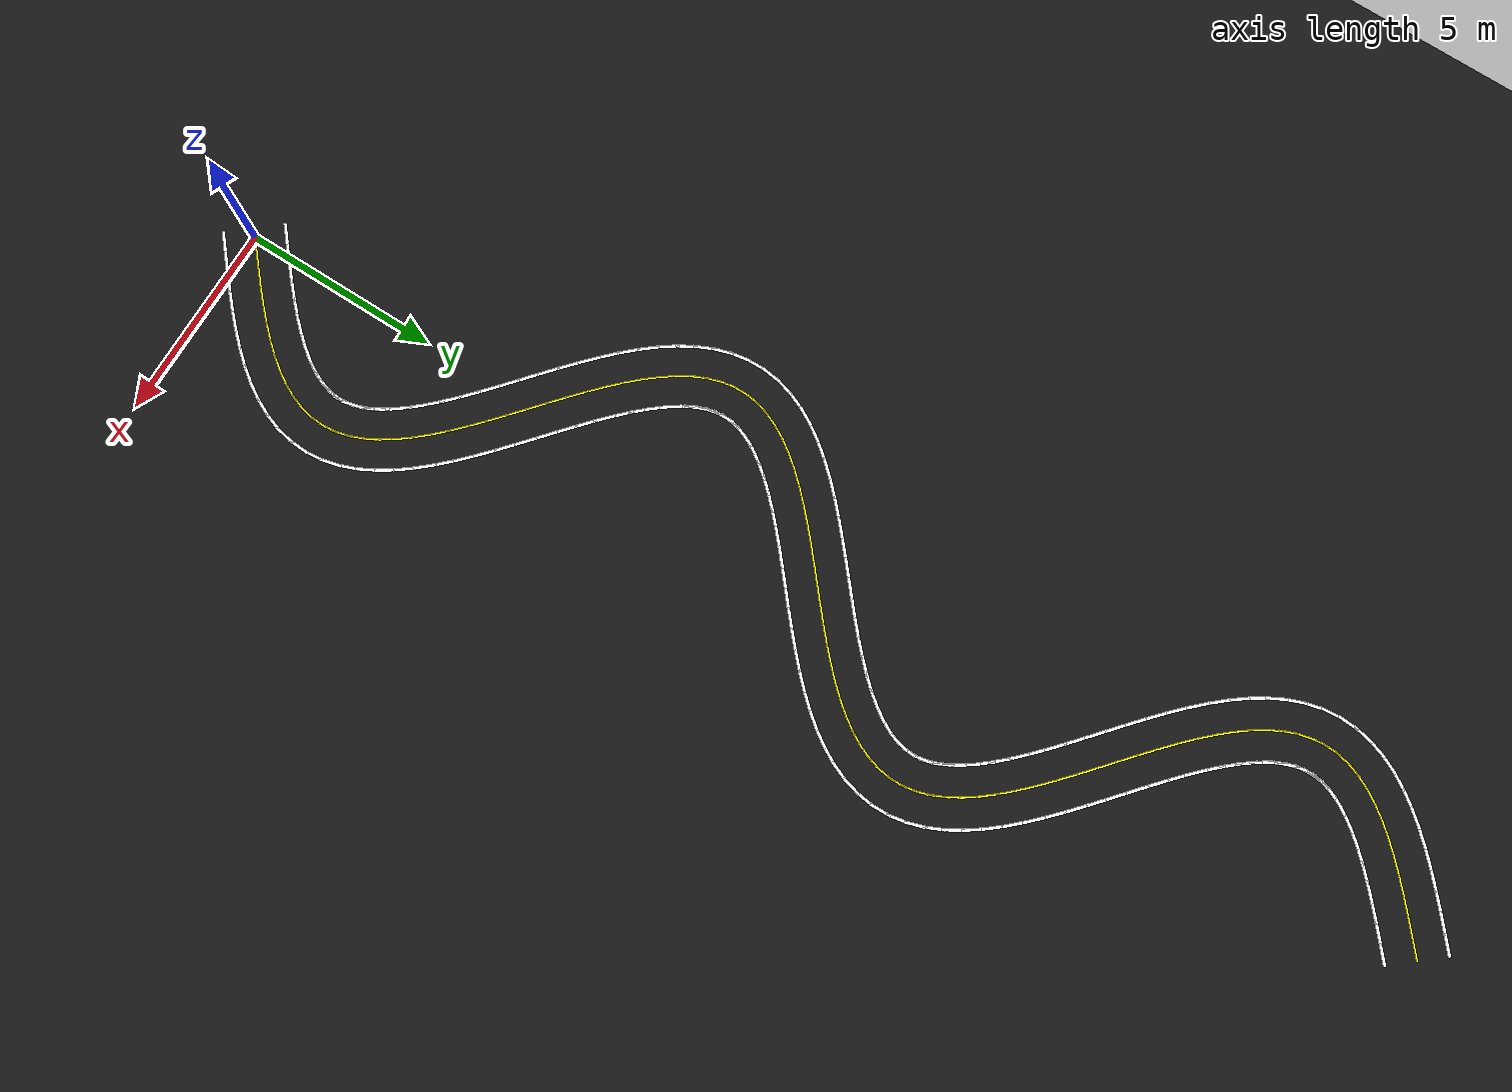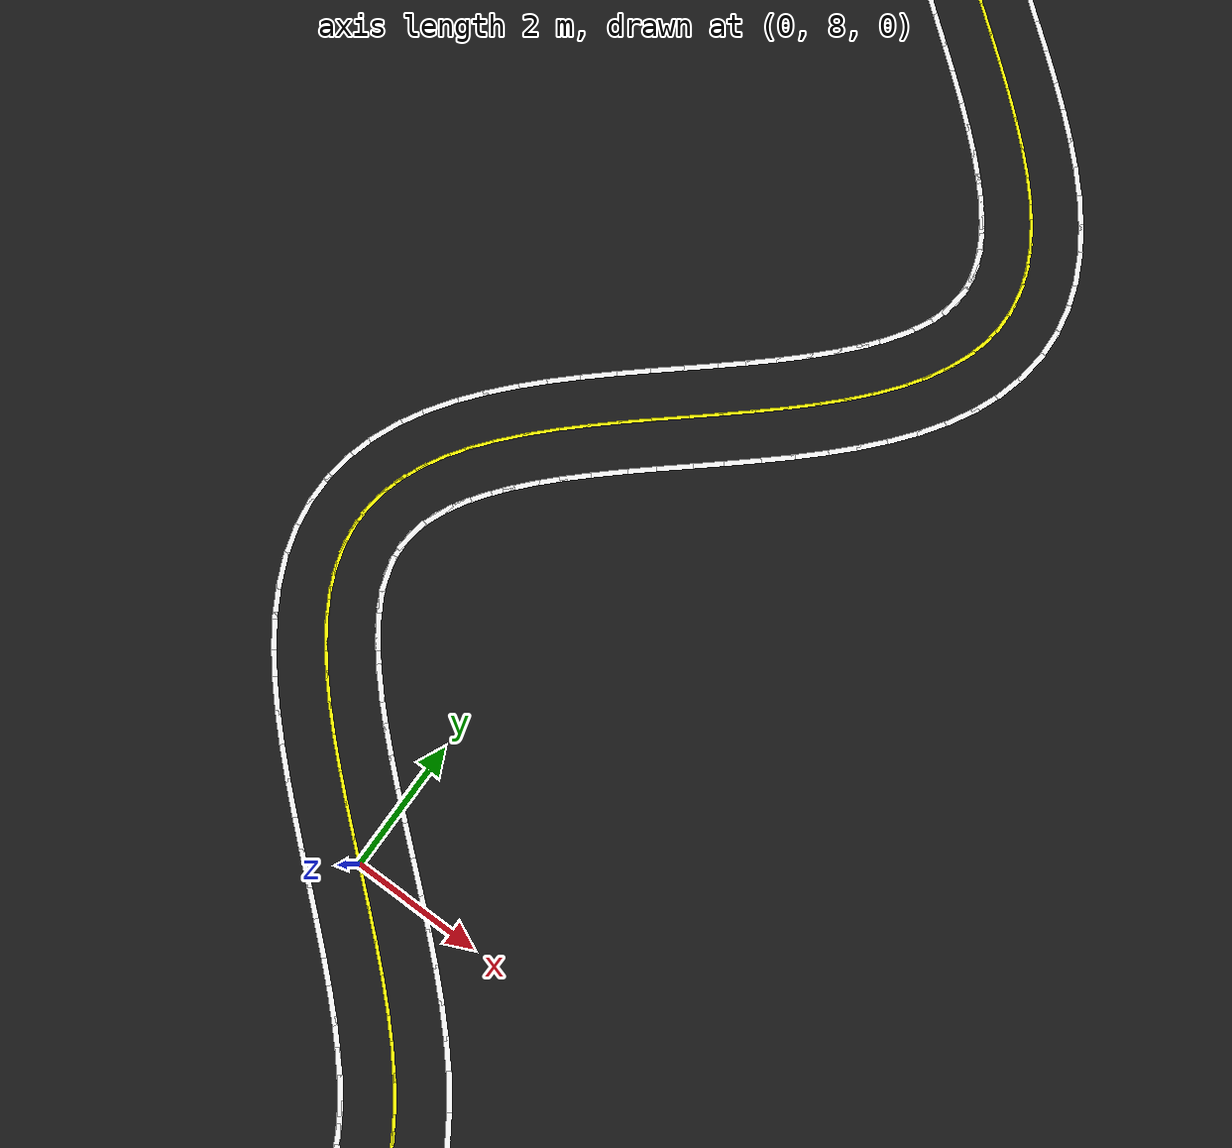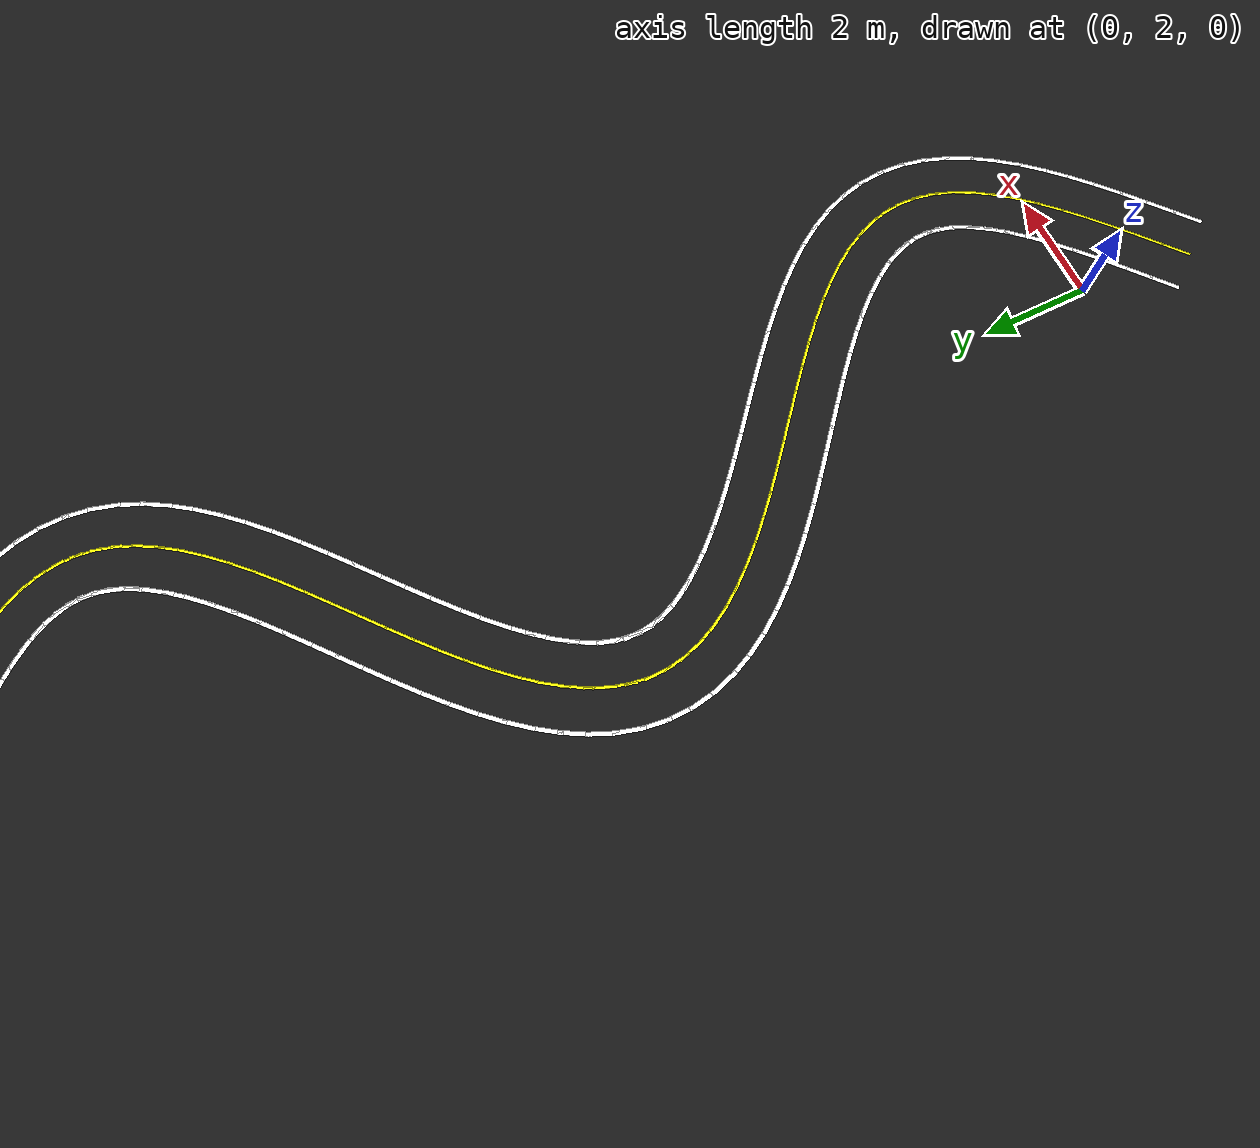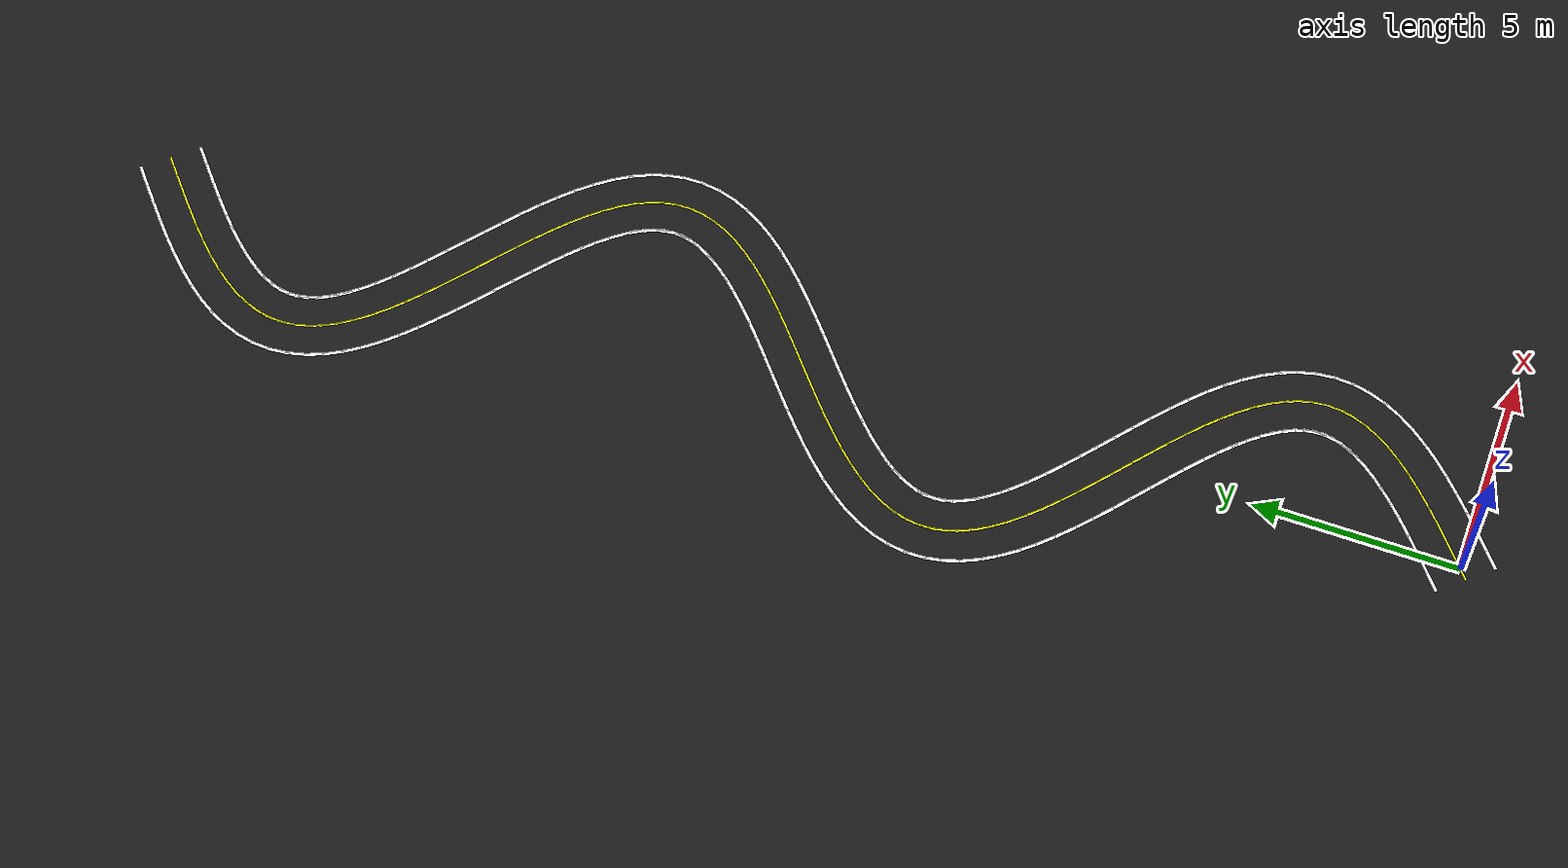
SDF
<?xml version="1.0"?>
<sdf version="1.6">
  <world name="double_s_lane_world">

    <plugin filename="ignition-gazebo-physics-system"
            name="ignition::gazebo::systems::Physics"/>
    <plugin filename="libignition-gazebo-sensors-system.so"
            name="ignition::gazebo::systems::Sensors">
      <render_engine>ogre2</render_engine>
    </plugin>
    <plugin filename="ignition-gazebo-scene-broadcaster-system"
            name="ignition::gazebo::systems::SceneBroadcaster"/>
    <plugin filename="ignition-gazebo-user-commands-system"
            name="ignition::gazebo::systems::UserCommands"/>

    <light type="directional" name="sun">
      <cast_shadows>true</cast_shadows>
      <pose>0 0 25 0 0 0</pose>
      <diffuse>0.85 0.85 0.85 1</diffuse>
      <specular>0.2 0.2 0.2 1</specular>
      <attenuation>
        <range>1000</range><constant>0.9</constant>
        <linear>0.01</linear><quadratic>0.001</quadratic>
      </attenuation>
      <direction>-0.5 0.1 -0.9</direction>
    </light>

    <!-- Dark asphalt ground -->
    <model name="ground">
      <static>true</static>
      <link name="link">
        <visual name="v">
          <geometry><plane><normal>0 0 1</normal><size>100 100</size></plane></geometry>
          <material>
            <ambient>0.10 0.10 0.10 1</ambient>
            <diffuse>0.10 0.10 0.10 1</diffuse>
          </material>
        </visual>
        <collision name="c">
          <geometry><plane><normal>0 0 1</normal><size>100 100</size></plane></geometry>
        </collision>
      </link>
    </model>

    <model name="seg_0000"><static>true</static>
      <pose>-0.4853 0.5718 0.002 0 0 0.7038</pose>
      <link name="link"><visual name="v">
        <geometry><box><size>0.550 0.080 0.0020</size></box></geometry>
        <material><ambient>1 1 1 1</ambient><diffuse>1 1 1 1</diffuse></material>
      </visual></link></model>
    <model name="seg_0001"><static>true</static>
      <pose>0.4853 -0.5718 0.002 0 0 0.7038</pose>
      <link name="link"><visual name="v">
        <geometry><box><size>0.550 0.080 0.0020</size></box></geometry>
        <material><ambient>1 1 1 1</ambient><diffuse>1 1 1 1</diffuse></material>
      </visual></link></model>
    <model name="seg_0002"><static>true</static>
      <pose>0.0000 0.0000 0.002 0 0 0.7038</pose>
      <link name="link"><visual name="v">
        <geometry><box><size>0.550 0.050 0.0020</size></box></geometry>
        <material><ambient>1 1 0 1</ambient><diffuse>1 1 0 1</diffuse></material>
      </visual></link></model>
    <model name="seg_0003"><static>true</static>
      <pose>-0.1078 0.8931 0.002 0 0 0.7078</pose>
      <link name="link"><visual name="v">
        <geometry><box><size>0.550 0.080 0.0020</size></box></geometry>
        <material><ambient>1 1 1 1</ambient><diffuse>1 1 1 1</diffuse></material>
      </visual></link></model>
    <model name="seg_0004"><static>true</static>
      <pose>0.8674 -0.2466 0.002 0 0 0.7078</pose>
      <link name="link"><visual name="v">
        <geometry><box><size>0.550 0.080 0.0020</size></box></geometry>
        <material><ambient>1 1 1 1</ambient><diffuse>1 1 1 1</diffuse></material>
      </visual></link></model>
    <model name="seg_0005"><static>true</static>
      <pose>0.3798 0.3232 0.002 0 0 0.7078</pose>
      <link name="link"><visual name="v">
        <geometry><box><size>0.550 0.050 0.0020</size></box></geometry>
        <material><ambient>1 1 0 1</ambient><diffuse>1 1 0 1</diffuse></material>
      </visual></link></model>
    <model name="seg_0006"><static>true</static>
      <pose>0.2589 1.2104 0.002 0 0 0.7199</pose>
      <link name="link"><visual name="v">
        <geometry><box><size>0.550 0.080 0.0020</size></box></geometry>
        <material><ambient>1 1 1 1</ambient><diffuse>1 1 1 1</diffuse></material>
      </visual></link></model>
    <model name="seg_0007"><static>true</static>
      <pose>1.2479 0.0826 0.002 0 0 0.7199</pose>
      <link name="link"><visual name="v">
        <geometry><box><size>0.550 0.080 0.0020</size></box></geometry>
        <material><ambient>1 1 1 1</ambient><diffuse>1 1 1 1</diffuse></material>
      </visual></link></model>
    <model name="seg_0008"><static>true</static>
      <pose>0.7534 0.6465 0.002 0 0 0.7199</pose>
      <link name="link"><visual name="v">
        <geometry><box><size>0.550 0.050 0.0020</size></box></geometry>
        <material><ambient>1 1 0 1</ambient><diffuse>1 1 0 1</diffuse></material>
      </visual></link></model>
    <model name="seg_0009"><static>true</static>
      <pose>0.6089 1.5232 0.002 0 0 0.7407</pose>
      <link name="link"><visual name="v">
        <geometry><box><size>0.550 0.080 0.0020</size></box></geometry>
        <material><ambient>1 1 1 1</ambient><diffuse>1 1 1 1</diffuse></material>
      </visual></link></model>
    <model name="seg_0010"><static>true</static>
      <pose>1.6211 0.4162 0.002 0 0 0.7407</pose>
      <link name="link"><visual name="v">
        <geometry><box><size>0.550 0.080 0.0020</size></box></geometry>
        <material><ambient>1 1 1 1</ambient><diffuse>1 1 1 1</diffuse></material>
      </visual></link></model>
    <model name="seg_0011"><static>true</static>
      <pose>1.1150 0.9697 0.002 0 0 0.7407</pose>
      <link name="link"><visual name="v">
        <geometry><box><size>0.550 0.050 0.0020</size></box></geometry>
        <material><ambient>1 1 0 1</ambient><diffuse>1 1 0 1</diffuse></material>
      </visual></link></model>
    <model name="seg_0012"><static>true</static>
      <pose>0.9360 1.8309 0.002 0 0 0.7709</pose>
      <link name="link"><visual name="v">
        <geometry><box><size>0.550 0.080 0.0020</size></box></geometry>
        <material><ambient>1 1 1 1</ambient><diffuse>1 1 1 1</diffuse></material>
      </visual></link></model>
    <model name="seg_0013"><static>true</static>
      <pose>1.9812 0.7550 0.002 0 0 0.7709</pose>
      <link name="link"><visual name="v">
        <geometry><box><size>0.550 0.080 0.0020</size></box></geometry>
        <material><ambient>1 1 1 1</ambient><diffuse>1 1 1 1</diffuse></material>
      </visual></link></model>
    <model name="seg_0014"><static>true</static>
      <pose>1.4586 1.2929 0.002 0 0 0.7709</pose>
      <link name="link"><visual name="v">
        <geometry><box><size>0.550 0.050 0.0020</size></box></geometry>
        <material><ambient>1 1 0 1</ambient><diffuse>1 1 0 1</diffuse></material>
      </visual></link></model>
    <model name="seg_0015"><static>true</static>
      <pose>1.2346 2.1323 0.002 0 0 0.8117</pose>
      <link name="link"><visual name="v">
        <geometry><box><size>0.550 0.080 0.0020</size></box></geometry>
        <material><ambient>1 1 1 1</ambient><diffuse>1 1 1 1</diffuse></material>
      </visual></link></model>
    <model name="seg_0016"><static>true</static>
      <pose>2.3228 1.1000 0.002 0 0 0.8117</pose>
      <link name="link"><visual name="v">
        <geometry><box><size>0.550 0.080 0.0020</size></box></geometry>
        <material><ambient>1 1 1 1</ambient><diffuse>1 1 1 1</diffuse></material>
      </visual></link></model>
    <model name="seg_0017"><static>true</static>
      <pose>1.7787 1.6162 0.002 0 0 0.8117</pose>
      <link name="link"><visual name="v">
        <geometry><box><size>0.550 0.050 0.0020</size></box></geometry>
        <material><ambient>1 1 0 1</ambient><diffuse>1 1 0 1</diffuse></material>
      </visual></link></model>
    <model name="seg_0018"><static>true</static>
      <pose>1.4995 2.4260 0.002 0 0 0.8648</pose>
      <link name="link"><visual name="v">
        <geometry><box><size>0.550 0.080 0.0020</size></box></geometry>
        <material><ambient>1 1 1 1</ambient><diffuse>1 1 1 1</diffuse></material>
      </visual></link></model>
    <model name="seg_0019"><static>true</static>
      <pose>2.6410 1.4528 0.002 0 0 0.8648</pose>
      <link name="link"><visual name="v">
        <geometry><box><size>0.550 0.080 0.0020</size></box></geometry>
        <material><ambient>1 1 1 1</ambient><diffuse>1 1 1 1</diffuse></material>
      </visual></link></model>
    <model name="seg_0020"><static>true</static>
      <pose>2.0702 1.9394 0.002 0 0 0.8648</pose>
      <link name="link"><visual name="v">
        <geometry><box><size>0.550 0.050 0.0020</size></box></geometry>
        <material><ambient>1 1 0 1</ambient><diffuse>1 1 0 1</diffuse></material>
      </visual></link></model>
    <model name="seg_0021"><static>true</static>
      <pose>1.7264 2.7099 0.002 0 0 0.9319</pose>
      <link name="link"><visual name="v">
        <geometry><box><size>0.550 0.080 0.0020</size></box></geometry>
        <material><ambient>1 1 1 1</ambient><diffuse>1 1 1 1</diffuse></material>
      </visual></link></model>
    <model name="seg_0022"><static>true</static>
      <pose>2.9305 1.8154 0.002 0 0 0.9319</pose>
      <link name="link"><visual name="v">
        <geometry><box><size>0.550 0.080 0.0020</size></box></geometry>
        <material><ambient>1 1 1 1</ambient><diffuse>1 1 1 1</diffuse></material>
      </visual></link></model>
    <model name="seg_0023"><static>true</static>
      <pose>2.3284 2.2626 0.002 0 0 0.9319</pose>
      <link name="link"><visual name="v">
        <geometry><box><size>0.550 0.050 0.0020</size></box></geometry>
        <material><ambient>1 1 0 1</ambient><diffuse>1 1 0 1</diffuse></material>
      </visual></link></model>
    <model name="seg_0024"><static>true</static>
      <pose>1.9121 2.9816 0.002 0 0 1.0150</pose>
      <link name="link"><visual name="v">
        <geometry><box><size>0.550 0.080 0.0020</size></box></geometry>
        <material><ambient>1 1 1 1</ambient><diffuse>1 1 1 1</diffuse></material>
      </visual></link></model>
    <model name="seg_0025"><static>true</static>
      <pose>3.1863 2.1901 0.002 0 0 1.0150</pose>
      <link name="link"><visual name="v">
        <geometry><box><size>0.550 0.080 0.0020</size></box></geometry>
        <material><ambient>1 1 1 1</ambient><diffuse>1 1 1 1</diffuse></material>
      </visual></link></model>
    <model name="seg_0026"><static>true</static>
      <pose>2.5492 2.5859 0.002 0 0 1.0150</pose>
      <link name="link"><visual name="v">
        <geometry><box><size>0.550 0.050 0.0020</size></box></geometry>
        <material><ambient>1 1 0 1</ambient><diffuse>1 1 0 1</diffuse></material>
      </visual></link></model>
    <model name="seg_0027"><static>true</static>
      <pose>2.0552 3.2388 0.002 0 0 1.1157</pose>
      <link name="link"><visual name="v">
        <geometry><box><size>0.550 0.080 0.0020</size></box></geometry>
        <material><ambient>1 1 1 1</ambient><diffuse>1 1 1 1</diffuse></material>
      </visual></link></model>
    <model name="seg_0028"><static>true</static>
      <pose>3.4025 2.5794 0.002 0 0 1.1157</pose>
      <link name="link"><visual name="v">
        <geometry><box><size>0.550 0.080 0.0020</size></box></geometry>
        <material><ambient>1 1 1 1</ambient><diffuse>1 1 1 1</diffuse></material>
      </visual></link></model>
    <model name="seg_0029"><static>true</static>
      <pose>2.7289 2.9091 0.002 0 0 1.1157</pose>
      <link name="link"><visual name="v">
        <geometry><box><size>0.550 0.050 0.0020</size></box></geometry>
        <material><ambient>1 1 0 1</ambient><diffuse>1 1 0 1</diffuse></material>
      </visual></link></model>
    <model name="seg_0030"><static>true</static>
      <pose>2.1568 3.4800 0.002 0 0 1.2343</pose>
      <link name="link"><visual name="v">
        <geometry><box><size>0.550 0.080 0.0020</size></box></geometry>
        <material><ambient>1 1 1 1</ambient><diffuse>1 1 1 1</diffuse></material>
      </visual></link></model>
    <model name="seg_0031"><static>true</static>
      <pose>3.5726 2.9847 0.002 0 0 1.2343</pose>
      <link name="link"><visual name="v">
        <geometry><box><size>0.550 0.080 0.0020</size></box></geometry>
        <material><ambient>1 1 1 1</ambient><diffuse>1 1 1 1</diffuse></material>
      </visual></link></model>
    <model name="seg_0032"><static>true</static>
      <pose>2.8647 3.2323 0.002 0 0 1.2343</pose>
      <link name="link"><visual name="v">
        <geometry><box><size>0.550 0.050 0.0020</size></box></geometry>
        <material><ambient>1 1 0 1</ambient><diffuse>1 1 0 1</diffuse></material>
      </visual></link></model>
    <model name="seg_0033"><static>true</static>
      <pose>2.2196 3.7059 0.002 0 0 1.3690</pose>
      <link name="link"><visual name="v">
        <geometry><box><size>0.550 0.080 0.0020</size></box></geometry>
        <material><ambient>1 1 1 1</ambient><diffuse>1 1 1 1</diffuse></material>
      </visual></link></model>
    <model name="seg_0034"><static>true</static>
      <pose>3.6892 3.4052 0.002 0 0 1.3690</pose>
      <link name="link"><visual name="v">
        <geometry><box><size>0.550 0.080 0.0020</size></box></geometry>
        <material><ambient>1 1 1 1</ambient><diffuse>1 1 1 1</diffuse></material>
      </visual></link></model>
    <model name="seg_0035"><static>true</static>
      <pose>2.9544 3.5556 0.002 0 0 1.3690</pose>
      <link name="link"><visual name="v">
        <geometry><box><size>0.550 0.050 0.0020</size></box></geometry>
        <material><ambient>1 1 0 1</ambient><diffuse>1 1 0 1</diffuse></material>
      </visual></link></model>
    <model name="seg_0036"><static>true</static>
      <pose>2.2478 3.9208 0.002 0 0 1.5148</pose>
      <link name="link"><visual name="v">
        <geometry><box><size>0.550 0.080 0.0020</size></box></geometry>
        <material><ambient>1 1 1 1</ambient><diffuse>1 1 1 1</diffuse></material>
      </visual></link></model>
    <model name="seg_0037"><static>true</static>
      <pose>3.7454 3.8368 0.002 0 0 1.5148</pose>
      <link name="link"><visual name="v">
        <geometry><box><size>0.550 0.080 0.0020</size></box></geometry>
        <material><ambient>1 1 1 1</ambient><diffuse>1 1 1 1</diffuse></material>
      </visual></link></model>
    <model name="seg_0038"><static>true</static>
      <pose>2.9966 3.8788 0.002 0 0 1.5148</pose>
      <link name="link"><visual name="v">
        <geometry><box><size>0.550 0.050 0.0020</size></box></geometry>
        <material><ambient>1 1 0 1</ambient><diffuse>1 1 0 1</diffuse></material>
      </visual></link></model>
    <model name="seg_0039"><static>true</static>
      <pose>2.2438 4.1323 0.002 0 0 1.6639</pose>
      <link name="link"><visual name="v">
        <geometry><box><size>0.550 0.080 0.0020</size></box></geometry>
        <material><ambient>1 1 1 1</ambient><diffuse>1 1 1 1</diffuse></material>
      </visual></link></model>
    <model name="seg_0040"><static>true</static>
      <pose>3.7373 4.2717 0.002 0 0 1.6639</pose>
      <link name="link"><visual name="v">
        <geometry><box><size>0.550 0.080 0.0020</size></box></geometry>
        <material><ambient>1 1 1 1</ambient><diffuse>1 1 1 1</diffuse></material>
      </visual></link></model>
    <model name="seg_0041"><static>true</static>
      <pose>2.9906 4.2020 0.002 0 0 1.6639</pose>
      <link name="link"><visual name="v">
        <geometry><box><size>0.550 0.050 0.0020</size></box></geometry>
        <material><ambient>1 1 0 1</ambient><diffuse>1 1 0 1</diffuse></material>
      </visual></link></model>
    <model name="seg_0042"><static>true</static>
      <pose>2.2073 4.3493 0.002 0 0 1.8076</pose>
      <link name="link"><visual name="v">
        <geometry><box><size>0.550 0.080 0.0020</size></box></geometry>
        <material><ambient>1 1 1 1</ambient><diffuse>1 1 1 1</diffuse></material>
      </visual></link></model>
    <model name="seg_0043"><static>true</static>
      <pose>3.6655 4.7012 0.002 0 0 1.8076</pose>
      <link name="link"><visual name="v">
        <geometry><box><size>0.550 0.080 0.0020</size></box></geometry>
        <material><ambient>1 1 1 1</ambient><diffuse>1 1 1 1</diffuse></material>
      </visual></link></model>
    <model name="seg_0044"><static>true</static>
      <pose>2.9364 4.5253 0.002 0 0 1.8076</pose>
      <link name="link"><visual name="v">
        <geometry><box><size>0.550 0.050 0.0020</size></box></geometry>
        <material><ambient>1 1 0 1</ambient><diffuse>1 1 0 1</diffuse></material>
      </visual></link></model>
    <model name="seg_0045"><static>true</static>
      <pose>2.1352 4.5788 0.002 0 0 1.9386</pose>
      <link name="link"><visual name="v">
        <geometry><box><size>0.550 0.080 0.0020</size></box></geometry>
        <material><ambient>1 1 1 1</ambient><diffuse>1 1 1 1</diffuse></material>
      </visual></link></model>
    <model name="seg_0046"><static>true</static>
      <pose>3.5348 5.1181 0.002 0 0 1.9386</pose>
      <link name="link"><visual name="v">
        <geometry><box><size>0.550 0.080 0.0020</size></box></geometry>
        <material><ambient>1 1 1 1</ambient><diffuse>1 1 1 1</diffuse></material>
      </visual></link></model>
    <model name="seg_0047"><static>true</static>
      <pose>2.8350 4.8485 0.002 0 0 1.9386</pose>
      <link name="link"><visual name="v">
        <geometry><box><size>0.550 0.050 0.0020</size></box></geometry>
        <material><ambient>1 1 0 1</ambient><diffuse>1 1 0 1</diffuse></material>
      </visual></link></model>
    <model name="seg_0048"><static>true</static>
      <pose>2.0234 4.8241 0.002 0 0 2.0528</pose>
      <link name="link"><visual name="v">
        <geometry><box><size>0.550 0.080 0.0020</size></box></geometry>
        <material><ambient>1 1 1 1</ambient><diffuse>1 1 1 1</diffuse></material>
      </visual></link></model>
    <model name="seg_0049"><static>true</static>
      <pose>3.3525 5.5194 0.002 0 0 2.0528</pose>
      <link name="link"><visual name="v">
        <geometry><box><size>0.550 0.080 0.0020</size></box></geometry>
        <material><ambient>1 1 1 1</ambient><diffuse>1 1 1 1</diffuse></material>
      </visual></link></model>
    <model name="seg_0050"><static>true</static>
      <pose>2.6880 5.1717 0.002 0 0 2.0528</pose>
      <link name="link"><visual name="v">
        <geometry><box><size>0.550 0.050 0.0020</size></box></geometry>
        <material><ambient>1 1 0 1</ambient><diffuse>1 1 0 1</diffuse></material>
      </visual></link></model>
    <model name="seg_0051"><static>true</static>
      <pose>1.8696 5.0851 0.002 0 0 2.1490</pose>
      <link name="link"><visual name="v">
        <geometry><box><size>0.550 0.080 0.0020</size></box></geometry>
        <material><ambient>1 1 1 1</ambient><diffuse>1 1 1 1</diffuse></material>
      </visual></link></model>
    <model name="seg_0052"><static>true</static>
      <pose>3.1258 5.9048 0.002 0 0 2.1490</pose>
      <link name="link"><visual name="v">
        <geometry><box><size>0.550 0.080 0.0020</size></box></geometry>
        <material><ambient>1 1 1 1</ambient><diffuse>1 1 1 1</diffuse></material>
      </visual></link></model>
    <model name="seg_0053"><static>true</static>
      <pose>2.4977 5.4949 0.002 0 0 2.1490</pose>
      <link name="link"><visual name="v">
        <geometry><box><size>0.550 0.050 0.0020</size></box></geometry>
        <material><ambient>1 1 0 1</ambient><diffuse>1 1 0 1</diffuse></material>
      </visual></link></model>
    <model name="seg_0054"><static>true</static>
      <pose>1.6734 5.3601 0.002 0 0 2.2279</pose>
      <link name="link"><visual name="v">
        <geometry><box><size>0.550 0.080 0.0020</size></box></geometry>
        <material><ambient>1 1 1 1</ambient><diffuse>1 1 1 1</diffuse></material>
      </visual></link></model>
    <model name="seg_0055"><static>true</static>
      <pose>2.8611 6.2763 0.002 0 0 2.2279</pose>
      <link name="link"><visual name="v">
        <geometry><box><size>0.550 0.080 0.0020</size></box></geometry>
        <material><ambient>1 1 1 1</ambient><diffuse>1 1 1 1</diffuse></material>
      </visual></link></model>
    <model name="seg_0056"><static>true</static>
      <pose>2.2672 5.8182 0.002 0 0 2.2279</pose>
      <link name="link"><visual name="v">
        <geometry><box><size>0.550 0.050 0.0020</size></box></geometry>
        <material><ambient>1 1 0 1</ambient><diffuse>1 1 0 1</diffuse></material>
      </visual></link></model>
    <model name="seg_0057"><static>true</static>
      <pose>1.4367 5.6466 0.002 0 0 2.2913</pose>
      <link name="link"><visual name="v">
        <geometry><box><size>0.550 0.080 0.0020</size></box></geometry>
        <material><ambient>1 1 1 1</ambient><diffuse>1 1 1 1</diffuse></material>
      </visual></link></model>
    <model name="seg_0058"><static>true</static>
      <pose>2.5639 6.6362 0.002 0 0 2.2913</pose>
      <link name="link"><visual name="v">
        <geometry><box><size>0.550 0.080 0.0020</size></box></geometry>
        <material><ambient>1 1 1 1</ambient><diffuse>1 1 1 1</diffuse></material>
      </visual></link></model>
    <model name="seg_0059"><static>true</static>
      <pose>2.0003 6.1414 0.002 0 0 2.2913</pose>
      <link name="link"><visual name="v">
        <geometry><box><size>0.550 0.050 0.0020</size></box></geometry>
        <material><ambient>1 1 0 1</ambient><diffuse>1 1 0 1</diffuse></material>
      </visual></link></model>
    <model name="seg_0060"><static>true</static>
      <pose>1.1629 5.9424 0.002 0 0 2.3412</pose>
      <link name="link"><visual name="v">
        <geometry><box><size>0.550 0.080 0.0020</size></box></geometry>
        <material><ambient>1 1 1 1</ambient><diffuse>1 1 1 1</diffuse></material>
      </visual></link></model>
    <model name="seg_0061"><static>true</static>
      <pose>2.2394 6.9869 0.002 0 0 2.3412</pose>
      <link name="link"><visual name="v">
        <geometry><box><size>0.550 0.080 0.0020</size></box></geometry>
        <material><ambient>1 1 1 1</ambient><diffuse>1 1 1 1</diffuse></material>
      </visual></link></model>
    <model name="seg_0062"><static>true</static>
      <pose>1.7012 6.4646 0.002 0 0 2.3412</pose>
      <link name="link"><visual name="v">
        <geometry><box><size>0.550 0.050 0.0020</size></box></geometry>
        <material><ambient>1 1 0 1</ambient><diffuse>1 1 0 1</diffuse></material>
      </visual></link></model>
    <model name="seg_0063"><static>true</static>
      <pose>0.8567 6.2455 0.002 0 0 2.3792</pose>
      <link name="link"><visual name="v">
        <geometry><box><size>0.550 0.080 0.0020</size></box></geometry>
        <material><ambient>1 1 1 1</ambient><diffuse>1 1 1 1</diffuse></material>
      </visual></link></model>
    <model name="seg_0064"><static>true</static>
      <pose>1.8927 7.3303 0.002 0 0 2.3792</pose>
      <link name="link"><visual name="v">
        <geometry><box><size>0.550 0.080 0.0020</size></box></geometry>
        <material><ambient>1 1 1 1</ambient><diffuse>1 1 1 1</diffuse></material>
      </visual></link></model>
    <model name="seg_0065"><static>true</static>
      <pose>1.3747 6.7879 0.002 0 0 2.3792</pose>
      <link name="link"><visual name="v">
        <geometry><box><size>0.550 0.050 0.0020</size></box></geometry>
        <material><ambient>1 1 0 1</ambient><diffuse>1 1 0 1</diffuse></material>
      </visual></link></model>
    <model name="seg_0066"><static>true</static>
      <pose>0.5233 6.5546 0.002 0 0 2.4070</pose>
      <link name="link"><visual name="v">
        <geometry><box><size>0.550 0.080 0.0020</size></box></geometry>
        <material><ambient>1 1 1 1</ambient><diffuse>1 1 1 1</diffuse></material>
      </visual></link></model>
    <model name="seg_0067"><static>true</static>
      <pose>1.5288 7.6677 0.002 0 0 2.4070</pose>
      <link name="link"><visual name="v">
        <geometry><box><size>0.550 0.080 0.0020</size></box></geometry>
        <material><ambient>1 1 1 1</ambient><diffuse>1 1 1 1</diffuse></material>
      </visual></link></model>
    <model name="seg_0068"><static>true</static>
      <pose>1.0261 7.1111 0.002 0 0 2.4070</pose>
      <link name="link"><visual name="v">
        <geometry><box><size>0.550 0.050 0.0020</size></box></geometry>
        <material><ambient>1 1 0 1</ambient><diffuse>1 1 0 1</diffuse></material>
      </visual></link></model>
    <model name="seg_0069"><static>true</static>
      <pose>0.1686 6.8686 0.002 0 0 2.4255</pose>
      <link name="link"><visual name="v">
        <geometry><box><size>0.550 0.080 0.0020</size></box></geometry>
        <material><ambient>1 1 1 1</ambient><diffuse>1 1 1 1</diffuse></material>
      </visual></link></model>
    <model name="seg_0070"><static>true</static>
      <pose>1.1533 8.0001 0.002 0 0 2.4255</pose>
      <link name="link"><visual name="v">
        <geometry><box><size>0.550 0.080 0.0020</size></box></geometry>
        <material><ambient>1 1 1 1</ambient><diffuse>1 1 1 1</diffuse></material>
      </visual></link></model>
    <model name="seg_0071"><static>true</static>
      <pose>0.6609 7.4343 0.002 0 0 2.4255</pose>
      <link name="link"><visual name="v">
        <geometry><box><size>0.550 0.050 0.0020</size></box></geometry>
        <material><ambient>1 1 0 1</ambient><diffuse>1 1 0 1</diffuse></material>
      </visual></link></model>
    <model name="seg_0072"><static>true</static>
      <pose>-0.2015 7.1869 0.002 0 0 2.4355</pose>
      <link name="link"><visual name="v">
        <geometry><box><size>0.550 0.080 0.0020</size></box></geometry>
        <material><ambient>1 1 1 1</ambient><diffuse>1 1 1 1</diffuse></material>
      </visual></link></model>
    <model name="seg_0073"><static>true</static>
      <pose>0.7718 8.3283 0.002 0 0 2.4355</pose>
      <link name="link"><visual name="v">
        <geometry><box><size>0.550 0.080 0.0020</size></box></geometry>
        <material><ambient>1 1 1 1</ambient><diffuse>1 1 1 1</diffuse></material>
      </visual></link></model>
    <model name="seg_0074"><static>true</static>
      <pose>0.2852 7.7576 0.002 0 0 2.4355</pose>
      <link name="link"><visual name="v">
        <geometry><box><size>0.550 0.050 0.0020</size></box></geometry>
        <material><ambient>1 1 0 1</ambient><diffuse>1 1 0 1</diffuse></material>
      </visual></link></model>
    <model name="seg_0075"><static>true</static>
      <pose>-0.5807 7.5091 0.002 0 0 2.4375</pose>
      <link name="link"><visual name="v">
        <geometry><box><size>0.550 0.080 0.0020</size></box></geometry>
        <material><ambient>1 1 1 1</ambient><diffuse>1 1 1 1</diffuse></material>
      </visual></link></model>
    <model name="seg_0076"><static>true</static>
      <pose>0.3903 8.6525 0.002 0 0 2.4375</pose>
      <link name="link"><visual name="v">
        <geometry><box><size>0.550 0.080 0.0020</size></box></geometry>
        <material><ambient>1 1 1 1</ambient><diffuse>1 1 1 1</diffuse></material>
      </visual></link></model>
    <model name="seg_0077"><static>true</static>
      <pose>-0.0952 8.0808 0.002 0 0 2.4375</pose>
      <link name="link"><visual name="v">
        <geometry><box><size>0.550 0.050 0.0020</size></box></geometry>
        <material><ambient>1 1 0 1</ambient><diffuse>1 1 0 1</diffuse></material>
      </visual></link></model>
    <model name="seg_0078"><static>true</static>
      <pose>-0.9629 7.8353 0.002 0 0 2.4315</pose>
      <link name="link"><visual name="v">
        <geometry><box><size>0.550 0.080 0.0020</size></box></geometry>
        <material><ambient>1 1 1 1</ambient><diffuse>1 1 1 1</diffuse></material>
      </visual></link></model>
    <model name="seg_0079"><static>true</static>
      <pose>0.0149 8.9728 0.002 0 0 2.4315</pose>
      <link name="link"><visual name="v">
        <geometry><box><size>0.550 0.080 0.0020</size></box></geometry>
        <material><ambient>1 1 1 1</ambient><diffuse>1 1 1 1</diffuse></material>
      </visual></link></model>
    <model name="seg_0080"><static>true</static>
      <pose>-0.4740 8.4040 0.002 0 0 2.4315</pose>
      <link name="link"><visual name="v">
        <geometry><box><size>0.550 0.050 0.0020</size></box></geometry>
        <material><ambient>1 1 0 1</ambient><diffuse>1 1 0 1</diffuse></material>
      </visual></link></model>
    <model name="seg_0081"><static>true</static>
      <pose>-1.3421 8.1655 0.002 0 0 2.4173</pose>
      <link name="link"><visual name="v">
        <geometry><box><size>0.550 0.080 0.0020</size></box></geometry>
        <material><ambient>1 1 1 1</ambient><diffuse>1 1 1 1</diffuse></material>
      </visual></link></model>
    <model name="seg_0082"><static>true</static>
      <pose>-0.3483 9.2890 0.002 0 0 2.4173</pose>
      <link name="link"><visual name="v">
        <geometry><box><size>0.550 0.080 0.0020</size></box></geometry>
        <material><ambient>1 1 1 1</ambient><diffuse>1 1 1 1</diffuse></material>
      </visual></link></model>
    <model name="seg_0083"><static>true</static>
      <pose>-0.8452 8.7273 0.002 0 0 2.4173</pose>
      <link name="link"><visual name="v">
        <geometry><box><size>0.550 0.050 0.0020</size></box></geometry>
        <material><ambient>1 1 0 1</ambient><diffuse>1 1 0 1</diffuse></material>
      </visual></link></model>
    <model name="seg_0084"><static>true</static>
      <pose>-1.7125 8.5004 0.002 0 0 2.3943</pose>
      <link name="link"><visual name="v">
        <geometry><box><size>0.550 0.080 0.0020</size></box></geometry>
        <material><ambient>1 1 1 1</ambient><diffuse>1 1 1 1</diffuse></material>
      </visual></link></model>
    <model name="seg_0085"><static>true</static>
      <pose>-0.6930 9.6007 0.002 0 0 2.3943</pose>
      <link name="link"><visual name="v">
        <geometry><box><size>0.550 0.080 0.0020</size></box></geometry>
        <material><ambient>1 1 1 1</ambient><diffuse>1 1 1 1</diffuse></material>
      </visual></link></model>
    <model name="seg_0086"><static>true</static>
      <pose>-1.2028 9.0505 0.002 0 0 2.3943</pose>
      <link name="link"><visual name="v">
        <geometry><box><size>0.550 0.050 0.0020</size></box></geometry>
        <material><ambient>1 1 0 1</ambient><diffuse>1 1 0 1</diffuse></material>
      </visual></link></model>
    <model name="seg_0087"><static>true</static>
      <pose>-2.0685 8.8406 0.002 0 0 2.3616</pose>
      <link name="link"><visual name="v">
        <geometry><box><size>0.550 0.080 0.0020</size></box></geometry>
        <material><ambient>1 1 1 1</ambient><diffuse>1 1 1 1</diffuse></material>
      </visual></link></model>
    <model name="seg_0088"><static>true</static>
      <pose>-1.0136 9.9069 0.002 0 0 2.3616</pose>
      <link name="link"><visual name="v">
        <geometry><box><size>0.550 0.080 0.0020</size></box></geometry>
        <material><ambient>1 1 1 1</ambient><diffuse>1 1 1 1</diffuse></material>
      </visual></link></model>
    <model name="seg_0089"><static>true</static>
      <pose>-1.5410 9.3737 0.002 0 0 2.3616</pose>
      <link name="link"><visual name="v">
        <geometry><box><size>0.550 0.050 0.0020</size></box></geometry>
        <material><ambient>1 1 0 1</ambient><diffuse>1 1 0 1</diffuse></material>
      </visual></link></model>
    <model name="seg_0090"><static>true</static>
      <pose>-2.4048 9.1874 0.002 0 0 2.3178</pose>
      <link name="link"><visual name="v">
        <geometry><box><size>0.550 0.080 0.0020</size></box></geometry>
        <material><ambient>1 1 1 1</ambient><diffuse>1 1 1 1</diffuse></material>
      </visual></link></model>
    <model name="seg_0091"><static>true</static>
      <pose>-1.3042 10.2066 0.002 0 0 2.3178</pose>
      <link name="link"><visual name="v">
        <geometry><box><size>0.550 0.080 0.0020</size></box></geometry>
        <material><ambient>1 1 1 1</ambient><diffuse>1 1 1 1</diffuse></material>
      </visual></link></model>
    <model name="seg_0092"><static>true</static>
      <pose>-1.8545 9.6970 0.002 0 0 2.3178</pose>
      <link name="link"><visual name="v">
        <geometry><box><size>0.550 0.050 0.0020</size></box></geometry>
        <material><ambient>1 1 0 1</ambient><diffuse>1 1 0 1</diffuse></material>
      </visual></link></model>
    <model name="seg_0093"><static>true</static>
      <pose>-2.7162 9.5424 0.002 0 0 2.2614</pose>
      <link name="link"><visual name="v">
        <geometry><box><size>0.550 0.080 0.0020</size></box></geometry>
        <material><ambient>1 1 1 1</ambient><diffuse>1 1 1 1</diffuse></material>
      </visual></link></model>
    <model name="seg_0094"><static>true</static>
      <pose>-1.5600 10.4980 0.002 0 0 2.2614</pose>
      <link name="link"><visual name="v">
        <geometry><box><size>0.550 0.080 0.0020</size></box></geometry>
        <material><ambient>1 1 1 1</ambient><diffuse>1 1 1 1</diffuse></material>
      </visual></link></model>
    <model name="seg_0095"><static>true</static>
      <pose>-2.1381 10.0202 0.002 0 0 2.2614</pose>
      <link name="link"><visual name="v">
        <geometry><box><size>0.550 0.050 0.0020</size></box></geometry>
        <material><ambient>1 1 0 1</ambient><diffuse>1 1 0 1</diffuse></material>
      </visual></link></model>
    <model name="seg_0096"><static>true</static>
      <pose>-2.9978 9.9078 0.002 0 0 2.1905</pose>
      <link name="link"><visual name="v">
        <geometry><box><size>0.550 0.080 0.0020</size></box></geometry>
        <material><ambient>1 1 1 1</ambient><diffuse>1 1 1 1</diffuse></material>
      </visual></link></model>
    <model name="seg_0097"><static>true</static>
      <pose>-1.7767 10.7790 0.002 0 0 2.1905</pose>
      <link name="link"><visual name="v">
        <geometry><box><size>0.550 0.080 0.0020</size></box></geometry>
        <material><ambient>1 1 1 1</ambient><diffuse>1 1 1 1</diffuse></material>
      </visual></link></model>
    <model name="seg_0098"><static>true</static>
      <pose>-2.3873 10.3434 0.002 0 0 2.1905</pose>
      <link name="link"><visual name="v">
        <geometry><box><size>0.550 0.050 0.0020</size></box></geometry>
        <material><ambient>1 1 0 1</ambient><diffuse>1 1 0 1</diffuse></material>
      </visual></link></model>
    <model name="seg_0099"><static>true</static>
      <pose>-3.2443 10.2860 0.002 0 0 2.1031</pose>
      <link name="link"><visual name="v">
        <geometry><box><size>0.550 0.080 0.0020</size></box></geometry>
        <material><ambient>1 1 1 1</ambient><diffuse>1 1 1 1</diffuse></material>
      </visual></link></model>
    <model name="seg_0100"><static>true</static>
      <pose>-1.9519 11.0473 0.002 0 0 2.1031</pose>
      <link name="link"><visual name="v">
        <geometry><box><size>0.550 0.080 0.0020</size></box></geometry>
        <material><ambient>1 1 1 1</ambient><diffuse>1 1 1 1</diffuse></material>
      </visual></link></model>
    <model name="seg_0101"><static>true</static>
      <pose>-2.5981 10.6667 0.002 0 0 2.1031</pose>
      <link name="link"><visual name="v">
        <geometry><box><size>0.550 0.050 0.0020</size></box></geometry>
        <material><ambient>1 1 0 1</ambient><diffuse>1 1 0 1</diffuse></material>
      </visual></link></model>
    <model name="seg_0102"><static>true</static>
      <pose>-3.4497 10.6792 0.002 0 0 1.9979</pose>
      <link name="link"><visual name="v">
        <geometry><box><size>0.550 0.080 0.0020</size></box></geometry>
        <material><ambient>1 1 1 1</ambient><diffuse>1 1 1 1</diffuse></material>
      </visual></link></model>
    <model name="seg_0103"><static>true</static>
      <pose>-2.0844 11.3006 0.002 0 0 1.9979</pose>
      <link name="link"><visual name="v">
        <geometry><box><size>0.550 0.080 0.0020</size></box></geometry>
        <material><ambient>1 1 1 1</ambient><diffuse>1 1 1 1</diffuse></material>
      </visual></link></model>
    <model name="seg_0104"><static>true</static>
      <pose>-2.7671 10.9899 0.002 0 0 1.9979</pose>
      <link name="link"><visual name="v">
        <geometry><box><size>0.550 0.050 0.0020</size></box></geometry>
        <material><ambient>1 1 0 1</ambient><diffuse>1 1 0 1</diffuse></material>
      </visual></link></model>
    <model name="seg_0105"><static>true</static>
      <pose>-3.6071 11.0885 0.002 0 0 1.8750</pose>
      <link name="link"><visual name="v">
        <geometry><box><size>0.550 0.080 0.0020</size></box></geometry>
        <material><ambient>1 1 1 1</ambient><diffuse>1 1 1 1</diffuse></material>
      </visual></link></model>
    <model name="seg_0106"><static>true</static>
      <pose>-2.1760 11.5378 0.002 0 0 1.8750</pose>
      <link name="link"><visual name="v">
        <geometry><box><size>0.550 0.080 0.0020</size></box></geometry>
        <material><ambient>1 1 1 1</ambient><diffuse>1 1 1 1</diffuse></material>
      </visual></link></model>
    <model name="seg_0107"><static>true</static>
      <pose>-2.8915 11.3131 0.002 0 0 1.8750</pose>
      <link name="link"><visual name="v">
        <geometry><box><size>0.550 0.050 0.0020</size></box></geometry>
        <material><ambient>1 1 0 1</ambient><diffuse>1 1 0 1</diffuse></material>
      </visual></link></model>
    <model name="seg_0108"><static>true</static>
      <pose>-3.7091 11.5123 0.002 0 0 1.7369</pose>
      <link name="link"><visual name="v">
        <geometry><box><size>0.550 0.080 0.0020</size></box></geometry>
        <material><ambient>1 1 1 1</ambient><diffuse>1 1 1 1</diffuse></material>
      </visual></link></model>
    <model name="seg_0109"><static>true</static>
      <pose>-2.2298 11.7604 0.002 0 0 1.7369</pose>
      <link name="link"><visual name="v">
        <geometry><box><size>0.550 0.080 0.0020</size></box></geometry>
        <material><ambient>1 1 1 1</ambient><diffuse>1 1 1 1</diffuse></material>
      </visual></link></model>
    <model name="seg_0110"><static>true</static>
      <pose>-2.9695 11.6364 0.002 0 0 1.7369</pose>
      <link name="link"><visual name="v">
        <geometry><box><size>0.550 0.050 0.0020</size></box></geometry>
        <material><ambient>1 1 0 1</ambient><diffuse>1 1 0 1</diffuse></material>
      </visual></link></model>
    <model name="seg_0111"><static>true</static>
      <pose>-3.7495 11.9456 0.002 0 0 1.5895</pose>
      <link name="link"><visual name="v">
        <geometry><box><size>0.550 0.080 0.0020</size></box></geometry>
        <material><ambient>1 1 1 1</ambient><diffuse>1 1 1 1</diffuse></material>
      </visual></link></model>
    <model name="seg_0112"><static>true</static>
      <pose>-2.2498 11.9736 0.002 0 0 1.5895</pose>
      <link name="link"><visual name="v">
        <geometry><box><size>0.550 0.080 0.0020</size></box></geometry>
        <material><ambient>1 1 1 1</ambient><diffuse>1 1 1 1</diffuse></material>
      </visual></link></model>
    <model name="seg_0113"><static>true</static>
      <pose>-2.9996 11.9596 0.002 0 0 1.5895</pose>
      <link name="link"><visual name="v">
        <geometry><box><size>0.550 0.050 0.0020</size></box></geometry>
        <material><ambient>1 1 0 1</ambient><diffuse>1 1 0 1</diffuse></material>
      </visual></link></model>
    <model name="seg_0114"><static>true</static>
      <pose>-3.7252 12.3799 0.002 0 0 1.4410</pose>
      <link name="link"><visual name="v">
        <geometry><box><size>0.550 0.080 0.0020</size></box></geometry>
        <material><ambient>1 1 1 1</ambient><diffuse>1 1 1 1</diffuse></material>
      </visual></link></model>
    <model name="seg_0115"><static>true</static>
      <pose>-2.2378 12.1857 0.002 0 0 1.4410</pose>
      <link name="link"><visual name="v">
        <geometry><box><size>0.550 0.080 0.0020</size></box></geometry>
        <material><ambient>1 1 1 1</ambient><diffuse>1 1 1 1</diffuse></material>
      </visual></link></model>
    <model name="seg_0116"><static>true</static>
      <pose>-2.9815 12.2828 0.002 0 0 1.4410</pose>
      <link name="link"><visual name="v">
        <geometry><box><size>0.550 0.050 0.0020</size></box></geometry>
        <material><ambient>1 1 0 1</ambient><diffuse>1 1 0 1</diffuse></material>
      </visual></link></model>
    <model name="seg_0117"><static>true</static>
      <pose>-3.6381 12.8068 0.002 0 0 1.2999</pose>
      <link name="link"><visual name="v">
        <geometry><box><size>0.550 0.080 0.0020</size></box></geometry>
        <material><ambient>1 1 1 1</ambient><diffuse>1 1 1 1</diffuse></material>
      </visual></link></model>
    <model name="seg_0118"><static>true</static>
      <pose>-2.1928 12.4053 0.002 0 0 1.2999</pose>
      <link name="link"><visual name="v">
        <geometry><box><size>0.550 0.080 0.0020</size></box></geometry>
        <material><ambient>1 1 1 1</ambient><diffuse>1 1 1 1</diffuse></material>
      </visual></link></model>
    <model name="seg_0119"><static>true</static>
      <pose>-2.9154 12.6061 0.002 0 0 1.2999</pose>
      <link name="link"><visual name="v">
        <geometry><box><size>0.550 0.050 0.0020</size></box></geometry>
        <material><ambient>1 1 0 1</ambient><diffuse>1 1 0 1</diffuse></material>
      </visual></link></model>
    <model name="seg_0120"><static>true</static>
      <pose>-3.4938 13.2200 0.002 0 0 1.1728</pose>
      <link name="link"><visual name="v">
        <geometry><box><size>0.550 0.080 0.0020</size></box></geometry>
        <material><ambient>1 1 1 1</ambient><diffuse>1 1 1 1</diffuse></material>
      </visual></link></model>
    <model name="seg_0121"><static>true</static>
      <pose>-2.1111 12.6386 0.002 0 0 1.1728</pose>
      <link name="link"><visual name="v">
        <geometry><box><size>0.550 0.080 0.0020</size></box></geometry>
        <material><ambient>1 1 1 1</ambient><diffuse>1 1 1 1</diffuse></material>
      </visual></link></model>
    <model name="seg_0122"><static>true</static>
      <pose>-2.8024 12.9293 0.002 0 0 1.1728</pose>
      <link name="link"><visual name="v">
        <geometry><box><size>0.550 0.050 0.0020</size></box></geometry>
        <material><ambient>1 1 0 1</ambient><diffuse>1 1 0 1</diffuse></material>
      </visual></link></model>
    <model name="seg_0123"><static>true</static>
      <pose>-3.2997 13.6172 0.002 0 0 1.0631</pose>
      <link name="link"><visual name="v">
        <geometry><box><size>0.550 0.080 0.0020</size></box></geometry>
        <material><ambient>1 1 1 1</ambient><diffuse>1 1 1 1</diffuse></material>
      </visual></link></model>
    <model name="seg_0124"><static>true</static>
      <pose>-1.9890 12.8879 0.002 0 0 1.0631</pose>
      <link name="link"><visual name="v">
        <geometry><box><size>0.550 0.080 0.0020</size></box></geometry>
        <material><ambient>1 1 1 1</ambient><diffuse>1 1 1 1</diffuse></material>
      </visual></link></model>
    <model name="seg_0125"><static>true</static>
      <pose>-2.6444 13.2525 0.002 0 0 1.0631</pose>
      <link name="link"><visual name="v">
        <geometry><box><size>0.550 0.050 0.0020</size></box></geometry>
        <material><ambient>1 1 0 1</ambient><diffuse>1 1 0 1</diffuse></material>
      </visual></link></model>
    <model name="seg_0126"><static>true</static>
      <pose>-3.0630 13.9989 0.002 0 0 0.9713</pose>
      <link name="link"><visual name="v">
        <geometry><box><size>0.550 0.080 0.0020</size></box></geometry>
        <material><ambient>1 1 1 1</ambient><diffuse>1 1 1 1</diffuse></material>
      </visual></link></model>
    <model name="seg_0127"><static>true</static>
      <pose>-1.8245 13.1526 0.002 0 0 0.9713</pose>
      <link name="link"><visual name="v">
        <geometry><box><size>0.550 0.080 0.0020</size></box></geometry>
        <material><ambient>1 1 1 1</ambient><diffuse>1 1 1 1</diffuse></material>
      </visual></link></model>
    <model name="seg_0128"><static>true</static>
      <pose>-2.4437 13.5758 0.002 0 0 0.9713</pose>
      <link name="link"><visual name="v">
        <geometry><box><size>0.550 0.050 0.0020</size></box></geometry>
        <material><ambient>1 1 0 1</ambient><diffuse>1 1 0 1</diffuse></material>
      </visual></link></model>
    <model name="seg_0129"><static>true</static>
      <pose>-2.7896 14.3673 0.002 0 0 0.8965</pose>
      <link name="link"><visual name="v">
        <geometry><box><size>0.550 0.080 0.0020</size></box></geometry>
        <material><ambient>1 1 1 1</ambient><diffuse>1 1 1 1</diffuse></material>
      </visual></link></model>
    <model name="seg_0130"><static>true</static>
      <pose>-1.6179 13.4307 0.002 0 0 0.8965</pose>
      <link name="link"><visual name="v">
        <geometry><box><size>0.550 0.080 0.0020</size></box></geometry>
        <material><ambient>1 1 1 1</ambient><diffuse>1 1 1 1</diffuse></material>
      </visual></link></model>
    <model name="seg_0131"><static>true</static>
      <pose>-2.2038 13.8990 0.002 0 0 0.8965</pose>
      <link name="link"><visual name="v">
        <geometry><box><size>0.550 0.050 0.0020</size></box></geometry>
        <material><ambient>1 1 0 1</ambient><diffuse>1 1 0 1</diffuse></material>
      </visual></link></model>
    <model name="seg_0132"><static>true</static>
      <pose>-2.4851 14.7247 0.002 0 0 0.8366</pose>
      <link name="link"><visual name="v">
        <geometry><box><size>0.550 0.080 0.0020</size></box></geometry>
        <material><ambient>1 1 1 1</ambient><diffuse>1 1 1 1</diffuse></material>
      </visual></link></model>
    <model name="seg_0133"><static>true</static>
      <pose>-1.3716 13.7197 0.002 0 0 0.8366</pose>
      <link name="link"><visual name="v">
        <geometry><box><size>0.550 0.080 0.0020</size></box></geometry>
        <material><ambient>1 1 1 1</ambient><diffuse>1 1 1 1</diffuse></material>
      </visual></link></model>
    <model name="seg_0134"><static>true</static>
      <pose>-1.9284 14.2222 0.002 0 0 0.8366</pose>
      <link name="link"><visual name="v">
        <geometry><box><size>0.550 0.050 0.0020</size></box></geometry>
        <material><ambient>1 1 0 1</ambient><diffuse>1 1 0 1</diffuse></material>
      </visual></link></model>
    <model name="seg_0135"><static>true</static>
      <pose>-2.1546 15.0734 0.002 0 0 0.7899</pose>
      <link name="link"><visual name="v">
        <geometry><box><size>0.550 0.080 0.0020</size></box></geometry>
        <material><ambient>1 1 1 1</ambient><diffuse>1 1 1 1</diffuse></material>
      </visual></link></model>
    <model name="seg_0136"><static>true</static>
      <pose>-1.0892 14.0175 0.002 0 0 0.7899</pose>
      <link name="link"><visual name="v">
        <geometry><box><size>0.550 0.080 0.0020</size></box></geometry>
        <material><ambient>1 1 1 1</ambient><diffuse>1 1 1 1</diffuse></material>
      </visual></link></model>
    <model name="seg_0137"><static>true</static>
      <pose>-1.6219 14.5455 0.002 0 0 0.7899</pose>
      <link name="link"><visual name="v">
        <geometry><box><size>0.550 0.050 0.0020</size></box></geometry>
        <material><ambient>1 1 0 1</ambient><diffuse>1 1 0 1</diffuse></material>
      </visual></link></model>
    <model name="seg_0138"><static>true</static>
      <pose>-1.8031 15.4151 0.002 0 0 0.7545</pose>
      <link name="link"><visual name="v">
        <geometry><box><size>0.550 0.080 0.0020</size></box></geometry>
        <material><ambient>1 1 1 1</ambient><diffuse>1 1 1 1</diffuse></material>
      </visual></link></model>
    <model name="seg_0139"><static>true</static>
      <pose>-0.7757 14.3222 0.002 0 0 0.7545</pose>
      <link name="link"><visual name="v">
        <geometry><box><size>0.550 0.080 0.0020</size></box></geometry>
        <material><ambient>1 1 1 1</ambient><diffuse>1 1 1 1</diffuse></material>
      </visual></link></model>
    <model name="seg_0140"><static>true</static>
      <pose>-1.2894 14.8687 0.002 0 0 0.7545</pose>
      <link name="link"><visual name="v">
        <geometry><box><size>0.550 0.050 0.0020</size></box></geometry>
        <material><ambient>1 1 0 1</ambient><diffuse>1 1 0 1</diffuse></material>
      </visual></link></model>
    <model name="seg_0141"><static>true</static>
      <pose>-1.4358 15.7512 0.002 0 0 0.7292</pose>
      <link name="link"><visual name="v">
        <geometry><box><size>0.550 0.080 0.0020</size></box></geometry>
        <material><ambient>1 1 1 1</ambient><diffuse>1 1 1 1</diffuse></material>
      </visual></link></model>
    <model name="seg_0142"><static>true</static>
      <pose>-0.4364 14.6326 0.002 0 0 0.7292</pose>
      <link name="link"><visual name="v">
        <geometry><box><size>0.550 0.080 0.0020</size></box></geometry>
        <material><ambient>1 1 1 1</ambient><diffuse>1 1 1 1</diffuse></material>
      </visual></link></model>
    <model name="seg_0143"><static>true</static>
      <pose>-0.9361 15.1919 0.002 0 0 0.7292</pose>
      <link name="link"><visual name="v">
        <geometry><box><size>0.550 0.050 0.0020</size></box></geometry>
        <material><ambient>1 1 0 1</ambient><diffuse>1 1 0 1</diffuse></material>
      </visual></link></model>
    <model name="seg_0144"><static>true</static>
      <pose>-1.0582 16.0825 0.002 0 0 0.7128</pose>
      <link name="link"><visual name="v">
        <geometry><box><size>0.550 0.080 0.0020</size></box></geometry>
        <material><ambient>1 1 1 1</ambient><diffuse>1 1 1 1</diffuse></material>
      </visual></link></model>
    <model name="seg_0145"><static>true</static>
      <pose>-0.0773 14.9478 0.002 0 0 0.7128</pose>
      <link name="link"><visual name="v">
        <geometry><box><size>0.550 0.080 0.0020</size></box></geometry>
        <material><ambient>1 1 1 1</ambient><diffuse>1 1 1 1</diffuse></material>
      </visual></link></model>
    <model name="seg_0146"><static>true</static>
      <pose>-0.5678 15.5152 0.002 0 0 0.7128</pose>
      <link name="link"><visual name="v">
        <geometry><box><size>0.550 0.050 0.0020</size></box></geometry>
        <material><ambient>1 1 0 1</ambient><diffuse>1 1 0 1</diffuse></material>
      </visual></link></model>
    <model name="seg_0147"><static>true</static>
      <pose>-0.6762 16.4097 0.002 0 0 0.7048</pose>
      <link name="link"><visual name="v">
        <geometry><box><size>0.550 0.080 0.0020</size></box></geometry>
        <material><ambient>1 1 1 1</ambient><diffuse>1 1 1 1</diffuse></material>
      </visual></link></model>
    <model name="seg_0148"><static>true</static>
      <pose>0.2956 15.2671 0.002 0 0 0.7048</pose>
      <link name="link"><visual name="v">
        <geometry><box><size>0.550 0.080 0.0020</size></box></geometry>
        <material><ambient>1 1 1 1</ambient><diffuse>1 1 1 1</diffuse></material>
      </visual></link></model>
    <model name="seg_0149"><static>true</static>
      <pose>-0.1903 15.8384 0.002 0 0 0.7048</pose>
      <link name="link"><visual name="v">
        <geometry><box><size>0.550 0.050 0.0020</size></box></geometry>
        <material><ambient>1 1 0 1</ambient><diffuse>1 1 0 1</diffuse></material>
      </visual></link></model>
    <model name="seg_0150"><static>true</static>
      <pose>-0.2956 16.7329 0.002 0 0 0.7048</pose>
      <link name="link"><visual name="v">
        <geometry><box><size>0.550 0.080 0.0020</size></box></geometry>
        <material><ambient>1 1 1 1</ambient><diffuse>1 1 1 1</diffuse></material>
      </visual></link></model>
    <model name="seg_0151"><static>true</static>
      <pose>0.6762 15.5903 0.002 0 0 0.7048</pose>
      <link name="link"><visual name="v">
        <geometry><box><size>0.550 0.080 0.0020</size></box></geometry>
        <material><ambient>1 1 1 1</ambient><diffuse>1 1 1 1</diffuse></material>
      </visual></link></model>
    <model name="seg_0152"><static>true</static>
      <pose>0.1903 16.1616 0.002 0 0 0.7048</pose>
      <link name="link"><visual name="v">
        <geometry><box><size>0.550 0.050 0.0020</size></box></geometry>
        <material><ambient>1 1 0 1</ambient><diffuse>1 1 0 1</diffuse></material>
      </visual></link></model>
    <model name="seg_0153"><static>true</static>
      <pose>0.0773 17.0522 0.002 0 0 0.7128</pose>
      <link name="link"><visual name="v">
        <geometry><box><size>0.550 0.080 0.0020</size></box></geometry>
        <material><ambient>1 1 1 1</ambient><diffuse>1 1 1 1</diffuse></material>
      </visual></link></model>
    <model name="seg_0154"><static>true</static>
      <pose>1.0582 15.9175 0.002 0 0 0.7128</pose>
      <link name="link"><visual name="v">
        <geometry><box><size>0.550 0.080 0.0020</size></box></geometry>
        <material><ambient>1 1 1 1</ambient><diffuse>1 1 1 1</diffuse></material>
      </visual></link></model>
    <model name="seg_0155"><static>true</static>
      <pose>0.5678 16.4848 0.002 0 0 0.7128</pose>
      <link name="link"><visual name="v">
        <geometry><box><size>0.550 0.050 0.0020</size></box></geometry>
        <material><ambient>1 1 0 1</ambient><diffuse>1 1 0 1</diffuse></material>
      </visual></link></model>
    <model name="seg_0156"><static>true</static>
      <pose>0.4364 17.3674 0.002 0 0 0.7292</pose>
      <link name="link"><visual name="v">
        <geometry><box><size>0.550 0.080 0.0020</size></box></geometry>
        <material><ambient>1 1 1 1</ambient><diffuse>1 1 1 1</diffuse></material>
      </visual></link></model>
    <model name="seg_0157"><static>true</static>
      <pose>1.4358 16.2488 0.002 0 0 0.7292</pose>
      <link name="link"><visual name="v">
        <geometry><box><size>0.550 0.080 0.0020</size></box></geometry>
        <material><ambient>1 1 1 1</ambient><diffuse>1 1 1 1</diffuse></material>
      </visual></link></model>
    <model name="seg_0158"><static>true</static>
      <pose>0.9361 16.8081 0.002 0 0 0.7292</pose>
      <link name="link"><visual name="v">
        <geometry><box><size>0.550 0.050 0.0020</size></box></geometry>
        <material><ambient>1 1 0 1</ambient><diffuse>1 1 0 1</diffuse></material>
      </visual></link></model>
    <model name="seg_0159"><static>true</static>
      <pose>0.7757 17.6778 0.002 0 0 0.7545</pose>
      <link name="link"><visual name="v">
        <geometry><box><size>0.550 0.080 0.0020</size></box></geometry>
        <material><ambient>1 1 1 1</ambient><diffuse>1 1 1 1</diffuse></material>
      </visual></link></model>
    <model name="seg_0160"><static>true</static>
      <pose>1.8031 16.5849 0.002 0 0 0.7545</pose>
      <link name="link"><visual name="v">
        <geometry><box><size>0.550 0.080 0.0020</size></box></geometry>
        <material><ambient>1 1 1 1</ambient><diffuse>1 1 1 1</diffuse></material>
      </visual></link></model>
    <model name="seg_0161"><static>true</static>
      <pose>1.2894 17.1313 0.002 0 0 0.7545</pose>
      <link name="link"><visual name="v">
        <geometry><box><size>0.550 0.050 0.0020</size></box></geometry>
        <material><ambient>1 1 0 1</ambient><diffuse>1 1 0 1</diffuse></material>
      </visual></link></model>
    <model name="seg_0162"><static>true</static>
      <pose>1.0892 17.9825 0.002 0 0 0.7899</pose>
      <link name="link"><visual name="v">
        <geometry><box><size>0.550 0.080 0.0020</size></box></geometry>
        <material><ambient>1 1 1 1</ambient><diffuse>1 1 1 1</diffuse></material>
      </visual></link></model>
    <model name="seg_0163"><static>true</static>
      <pose>2.1546 16.9266 0.002 0 0 0.7899</pose>
      <link name="link"><visual name="v">
        <geometry><box><size>0.550 0.080 0.0020</size></box></geometry>
        <material><ambient>1 1 1 1</ambient><diffuse>1 1 1 1</diffuse></material>
      </visual></link></model>
    <model name="seg_0164"><static>true</static>
      <pose>1.6219 17.4545 0.002 0 0 0.7899</pose>
      <link name="link"><visual name="v">
        <geometry><box><size>0.550 0.050 0.0020</size></box></geometry>
        <material><ambient>1 1 0 1</ambient><diffuse>1 1 0 1</diffuse></material>
      </visual></link></model>
    <model name="seg_0165"><static>true</static>
      <pose>1.3716 18.2803 0.002 0 0 0.8366</pose>
      <link name="link"><visual name="v">
        <geometry><box><size>0.550 0.080 0.0020</size></box></geometry>
        <material><ambient>1 1 1 1</ambient><diffuse>1 1 1 1</diffuse></material>
      </visual></link></model>
    <model name="seg_0166"><static>true</static>
      <pose>2.4851 17.2753 0.002 0 0 0.8366</pose>
      <link name="link"><visual name="v">
        <geometry><box><size>0.550 0.080 0.0020</size></box></geometry>
        <material><ambient>1 1 1 1</ambient><diffuse>1 1 1 1</diffuse></material>
      </visual></link></model>
    <model name="seg_0167"><static>true</static>
      <pose>1.9284 17.7778 0.002 0 0 0.8366</pose>
      <link name="link"><visual name="v">
        <geometry><box><size>0.550 0.050 0.0020</size></box></geometry>
        <material><ambient>1 1 0 1</ambient><diffuse>1 1 0 1</diffuse></material>
      </visual></link></model>
    <model name="seg_0168"><static>true</static>
      <pose>1.6179 18.5693 0.002 0 0 0.8965</pose>
      <link name="link"><visual name="v">
        <geometry><box><size>0.550 0.080 0.0020</size></box></geometry>
        <material><ambient>1 1 1 1</ambient><diffuse>1 1 1 1</diffuse></material>
      </visual></link></model>
    <model name="seg_0169"><static>true</static>
      <pose>2.7896 17.6327 0.002 0 0 0.8965</pose>
      <link name="link"><visual name="v">
        <geometry><box><size>0.550 0.080 0.0020</size></box></geometry>
        <material><ambient>1 1 1 1</ambient><diffuse>1 1 1 1</diffuse></material>
      </visual></link></model>
    <model name="seg_0170"><static>true</static>
      <pose>2.2038 18.1010 0.002 0 0 0.8965</pose>
      <link name="link"><visual name="v">
        <geometry><box><size>0.550 0.050 0.0020</size></box></geometry>
        <material><ambient>1 1 0 1</ambient><diffuse>1 1 0 1</diffuse></material>
      </visual></link></model>
    <model name="seg_0171"><static>true</static>
      <pose>1.8245 18.8474 0.002 0 0 0.9713</pose>
      <link name="link"><visual name="v">
        <geometry><box><size>0.550 0.080 0.0020</size></box></geometry>
        <material><ambient>1 1 1 1</ambient><diffuse>1 1 1 1</diffuse></material>
      </visual></link></model>
    <model name="seg_0172"><static>true</static>
      <pose>3.0630 18.0011 0.002 0 0 0.9713</pose>
      <link name="link"><visual name="v">
        <geometry><box><size>0.550 0.080 0.0020</size></box></geometry>
        <material><ambient>1 1 1 1</ambient><diffuse>1 1 1 1</diffuse></material>
      </visual></link></model>
    <model name="seg_0173"><static>true</static>
      <pose>2.4437 18.4242 0.002 0 0 0.9713</pose>
      <link name="link"><visual name="v">
        <geometry><box><size>0.550 0.050 0.0020</size></box></geometry>
        <material><ambient>1 1 0 1</ambient><diffuse>1 1 0 1</diffuse></material>
      </visual></link></model>
    <model name="seg_0174"><static>true</static>
      <pose>1.9890 19.1121 0.002 0 0 1.0631</pose>
      <link name="link"><visual name="v">
        <geometry><box><size>0.550 0.080 0.0020</size></box></geometry>
        <material><ambient>1 1 1 1</ambient><diffuse>1 1 1 1</diffuse></material>
      </visual></link></model>
    <model name="seg_0175"><static>true</static>
      <pose>3.2997 18.3828 0.002 0 0 1.0631</pose>
      <link name="link"><visual name="v">
        <geometry><box><size>0.550 0.080 0.0020</size></box></geometry>
        <material><ambient>1 1 1 1</ambient><diffuse>1 1 1 1</diffuse></material>
      </visual></link></model>
    <model name="seg_0176"><static>true</static>
      <pose>2.6444 18.7475 0.002 0 0 1.0631</pose>
      <link name="link"><visual name="v">
        <geometry><box><size>0.550 0.050 0.0020</size></box></geometry>
        <material><ambient>1 1 0 1</ambient><diffuse>1 1 0 1</diffuse></material>
      </visual></link></model>
    <model name="seg_0177"><static>true</static>
      <pose>2.1111 19.3614 0.002 0 0 1.1728</pose>
      <link name="link"><visual name="v">
        <geometry><box><size>0.550 0.080 0.0020</size></box></geometry>
        <material><ambient>1 1 1 1</ambient><diffuse>1 1 1 1</diffuse></material>
      </visual></link></model>
    <model name="seg_0178"><static>true</static>
      <pose>3.4938 18.7800 0.002 0 0 1.1728</pose>
      <link name="link"><visual name="v">
        <geometry><box><size>0.550 0.080 0.0020</size></box></geometry>
        <material><ambient>1 1 1 1</ambient><diffuse>1 1 1 1</diffuse></material>
      </visual></link></model>
    <model name="seg_0179"><static>true</static>
      <pose>2.8024 19.0707 0.002 0 0 1.1728</pose>
      <link name="link"><visual name="v">
        <geometry><box><size>0.550 0.050 0.0020</size></box></geometry>
        <material><ambient>1 1 0 1</ambient><diffuse>1 1 0 1</diffuse></material>
      </visual></link></model>
    <model name="seg_0180"><static>true</static>
      <pose>2.1928 19.5947 0.002 0 0 1.2999</pose>
      <link name="link"><visual name="v">
        <geometry><box><size>0.550 0.080 0.0020</size></box></geometry>
        <material><ambient>1 1 1 1</ambient><diffuse>1 1 1 1</diffuse></material>
      </visual></link></model>
    <model name="seg_0181"><static>true</static>
      <pose>3.6381 19.1932 0.002 0 0 1.2999</pose>
      <link name="link"><visual name="v">
        <geometry><box><size>0.550 0.080 0.0020</size></box></geometry>
        <material><ambient>1 1 1 1</ambient><diffuse>1 1 1 1</diffuse></material>
      </visual></link></model>
    <model name="seg_0182"><static>true</static>
      <pose>2.9154 19.3939 0.002 0 0 1.2999</pose>
      <link name="link"><visual name="v">
        <geometry><box><size>0.550 0.050 0.0020</size></box></geometry>
        <material><ambient>1 1 0 1</ambient><diffuse>1 1 0 1</diffuse></material>
      </visual></link></model>
    <model name="seg_0183"><static>true</static>
      <pose>2.2378 19.8143 0.002 0 0 1.4410</pose>
      <link name="link"><visual name="v">
        <geometry><box><size>0.550 0.080 0.0020</size></box></geometry>
        <material><ambient>1 1 1 1</ambient><diffuse>1 1 1 1</diffuse></material>
      </visual></link></model>
    <model name="seg_0184"><static>true</static>
      <pose>3.7252 19.6201 0.002 0 0 1.4410</pose>
      <link name="link"><visual name="v">
        <geometry><box><size>0.550 0.080 0.0020</size></box></geometry>
        <material><ambient>1 1 1 1</ambient><diffuse>1 1 1 1</diffuse></material>
      </visual></link></model>
    <model name="seg_0185"><static>true</static>
      <pose>2.9815 19.7172 0.002 0 0 1.4410</pose>
      <link name="link"><visual name="v">
        <geometry><box><size>0.550 0.050 0.0020</size></box></geometry>
        <material><ambient>1 1 0 1</ambient><diffuse>1 1 0 1</diffuse></material>
      </visual></link></model>
    <model name="seg_0186"><static>true</static>
      <pose>2.2498 20.0264 0.002 0 0 1.5895</pose>
      <link name="link"><visual name="v">
        <geometry><box><size>0.550 0.080 0.0020</size></box></geometry>
        <material><ambient>1 1 1 1</ambient><diffuse>1 1 1 1</diffuse></material>
      </visual></link></model>
    <model name="seg_0187"><static>true</static>
      <pose>3.7495 20.0544 0.002 0 0 1.5895</pose>
      <link name="link"><visual name="v">
        <geometry><box><size>0.550 0.080 0.0020</size></box></geometry>
        <material><ambient>1 1 1 1</ambient><diffuse>1 1 1 1</diffuse></material>
      </visual></link></model>
    <model name="seg_0188"><static>true</static>
      <pose>2.9996 20.0404 0.002 0 0 1.5895</pose>
      <link name="link"><visual name="v">
        <geometry><box><size>0.550 0.050 0.0020</size></box></geometry>
        <material><ambient>1 1 0 1</ambient><diffuse>1 1 0 1</diffuse></material>
      </visual></link></model>
    <model name="seg_0189"><static>true</static>
      <pose>2.2298 20.2396 0.002 0 0 1.7369</pose>
      <link name="link"><visual name="v">
        <geometry><box><size>0.550 0.080 0.0020</size></box></geometry>
        <material><ambient>1 1 1 1</ambient><diffuse>1 1 1 1</diffuse></material>
      </visual></link></model>
    <model name="seg_0190"><static>true</static>
      <pose>3.7091 20.4877 0.002 0 0 1.7369</pose>
      <link name="link"><visual name="v">
        <geometry><box><size>0.550 0.080 0.0020</size></box></geometry>
        <material><ambient>1 1 1 1</ambient><diffuse>1 1 1 1</diffuse></material>
      </visual></link></model>
    <model name="seg_0191"><static>true</static>
      <pose>2.9695 20.3636 0.002 0 0 1.7369</pose>
      <link name="link"><visual name="v">
        <geometry><box><size>0.550 0.050 0.0020</size></box></geometry>
        <material><ambient>1 1 0 1</ambient><diffuse>1 1 0 1</diffuse></material>
      </visual></link></model>
    <model name="seg_0192"><static>true</static>
      <pose>2.1760 20.4622 0.002 0 0 1.8750</pose>
      <link name="link"><visual name="v">
        <geometry><box><size>0.550 0.080 0.0020</size></box></geometry>
        <material><ambient>1 1 1 1</ambient><diffuse>1 1 1 1</diffuse></material>
      </visual></link></model>
    <model name="seg_0193"><static>true</static>
      <pose>3.6071 20.9115 0.002 0 0 1.8750</pose>
      <link name="link"><visual name="v">
        <geometry><box><size>0.550 0.080 0.0020</size></box></geometry>
        <material><ambient>1 1 1 1</ambient><diffuse>1 1 1 1</diffuse></material>
      </visual></link></model>
    <model name="seg_0194"><static>true</static>
      <pose>2.8915 20.6869 0.002 0 0 1.8750</pose>
      <link name="link"><visual name="v">
        <geometry><box><size>0.550 0.050 0.0020</size></box></geometry>
        <material><ambient>1 1 0 1</ambient><diffuse>1 1 0 1</diffuse></material>
      </visual></link></model>
    <model name="seg_0195"><static>true</static>
      <pose>2.0844 20.6994 0.002 0 0 1.9979</pose>
      <link name="link"><visual name="v">
        <geometry><box><size>0.550 0.080 0.0020</size></box></geometry>
        <material><ambient>1 1 1 1</ambient><diffuse>1 1 1 1</diffuse></material>
      </visual></link></model>
    <model name="seg_0196"><static>true</static>
      <pose>3.4497 21.3208 0.002 0 0 1.9979</pose>
      <link name="link"><visual name="v">
        <geometry><box><size>0.550 0.080 0.0020</size></box></geometry>
        <material><ambient>1 1 1 1</ambient><diffuse>1 1 1 1</diffuse></material>
      </visual></link></model>
    <model name="seg_0197"><static>true</static>
      <pose>2.7671 21.0101 0.002 0 0 1.9979</pose>
      <link name="link"><visual name="v">
        <geometry><box><size>0.550 0.050 0.0020</size></box></geometry>
        <material><ambient>1 1 0 1</ambient><diffuse>1 1 0 1</diffuse></material>
      </visual></link></model>
    <model name="seg_0198"><static>true</static>
      <pose>1.9519 20.9527 0.002 0 0 2.1031</pose>
      <link name="link"><visual name="v">
        <geometry><box><size>0.550 0.080 0.0020</size></box></geometry>
        <material><ambient>1 1 1 1</ambient><diffuse>1 1 1 1</diffuse></material>
      </visual></link></model>
    <model name="seg_0199"><static>true</static>
      <pose>3.2443 21.7140 0.002 0 0 2.1031</pose>
      <link name="link"><visual name="v">
        <geometry><box><size>0.550 0.080 0.0020</size></box></geometry>
        <material><ambient>1 1 1 1</ambient><diffuse>1 1 1 1</diffuse></material>
      </visual></link></model>
    <model name="seg_0200"><static>true</static>
      <pose>2.5981 21.3333 0.002 0 0 2.1031</pose>
      <link name="link"><visual name="v">
        <geometry><box><size>0.550 0.050 0.0020</size></box></geometry>
        <material><ambient>1 1 0 1</ambient><diffuse>1 1 0 1</diffuse></material>
      </visual></link></model>
    <model name="seg_0201"><static>true</static>
      <pose>1.7767 21.2210 0.002 0 0 2.1905</pose>
      <link name="link"><visual name="v">
        <geometry><box><size>0.550 0.080 0.0020</size></box></geometry>
        <material><ambient>1 1 1 1</ambient><diffuse>1 1 1 1</diffuse></material>
      </visual></link></model>
    <model name="seg_0202"><static>true</static>
      <pose>2.9978 22.0922 0.002 0 0 2.1905</pose>
      <link name="link"><visual name="v">
        <geometry><box><size>0.550 0.080 0.0020</size></box></geometry>
        <material><ambient>1 1 1 1</ambient><diffuse>1 1 1 1</diffuse></material>
      </visual></link></model>
    <model name="seg_0203"><static>true</static>
      <pose>2.3873 21.6566 0.002 0 0 2.1905</pose>
      <link name="link"><visual name="v">
        <geometry><box><size>0.550 0.050 0.0020</size></box></geometry>
        <material><ambient>1 1 0 1</ambient><diffuse>1 1 0 1</diffuse></material>
      </visual></link></model>
    <model name="seg_0204"><static>true</static>
      <pose>1.5600 21.5020 0.002 0 0 2.2614</pose>
      <link name="link"><visual name="v">
        <geometry><box><size>0.550 0.080 0.0020</size></box></geometry>
        <material><ambient>1 1 1 1</ambient><diffuse>1 1 1 1</diffuse></material>
      </visual></link></model>
    <model name="seg_0205"><static>true</static>
      <pose>2.7162 22.4576 0.002 0 0 2.2614</pose>
      <link name="link"><visual name="v">
        <geometry><box><size>0.550 0.080 0.0020</size></box></geometry>
        <material><ambient>1 1 1 1</ambient><diffuse>1 1 1 1</diffuse></material>
      </visual></link></model>
    <model name="seg_0206"><static>true</static>
      <pose>2.1381 21.9798 0.002 0 0 2.2614</pose>
      <link name="link"><visual name="v">
        <geometry><box><size>0.550 0.050 0.0020</size></box></geometry>
        <material><ambient>1 1 0 1</ambient><diffuse>1 1 0 1</diffuse></material>
      </visual></link></model>
    <model name="seg_0207"><static>true</static>
      <pose>1.3042 21.7934 0.002 0 0 2.3178</pose>
      <link name="link"><visual name="v">
        <geometry><box><size>0.550 0.080 0.0020</size></box></geometry>
        <material><ambient>1 1 1 1</ambient><diffuse>1 1 1 1</diffuse></material>
      </visual></link></model>
    <model name="seg_0208"><static>true</static>
      <pose>2.4048 22.8126 0.002 0 0 2.3178</pose>
      <link name="link"><visual name="v">
        <geometry><box><size>0.550 0.080 0.0020</size></box></geometry>
        <material><ambient>1 1 1 1</ambient><diffuse>1 1 1 1</diffuse></material>
      </visual></link></model>
    <model name="seg_0209"><static>true</static>
      <pose>1.8545 22.3030 0.002 0 0 2.3178</pose>
      <link name="link"><visual name="v">
        <geometry><box><size>0.550 0.050 0.0020</size></box></geometry>
        <material><ambient>1 1 0 1</ambient><diffuse>1 1 0 1</diffuse></material>
      </visual></link></model>
    <model name="seg_0210"><static>true</static>
      <pose>1.0136 22.0931 0.002 0 0 2.3616</pose>
      <link name="link"><visual name="v">
        <geometry><box><size>0.550 0.080 0.0020</size></box></geometry>
        <material><ambient>1 1 1 1</ambient><diffuse>1 1 1 1</diffuse></material>
      </visual></link></model>
    <model name="seg_0211"><static>true</static>
      <pose>2.0685 23.1594 0.002 0 0 2.3616</pose>
      <link name="link"><visual name="v">
        <geometry><box><size>0.550 0.080 0.0020</size></box></geometry>
        <material><ambient>1 1 1 1</ambient><diffuse>1 1 1 1</diffuse></material>
      </visual></link></model>
    <model name="seg_0212"><static>true</static>
      <pose>1.5410 22.6263 0.002 0 0 2.3616</pose>
      <link name="link"><visual name="v">
        <geometry><box><size>0.550 0.050 0.0020</size></box></geometry>
        <material><ambient>1 1 0 1</ambient><diffuse>1 1 0 1</diffuse></material>
      </visual></link></model>
    <model name="seg_0213"><static>true</static>
      <pose>0.6930 22.3993 0.002 0 0 2.3943</pose>
      <link name="link"><visual name="v">
        <geometry><box><size>0.550 0.080 0.0020</size></box></geometry>
        <material><ambient>1 1 1 1</ambient><diffuse>1 1 1 1</diffuse></material>
      </visual></link></model>
    <model name="seg_0214"><static>true</static>
      <pose>1.7125 23.4996 0.002 0 0 2.3943</pose>
      <link name="link"><visual name="v">
        <geometry><box><size>0.550 0.080 0.0020</size></box></geometry>
        <material><ambient>1 1 1 1</ambient><diffuse>1 1 1 1</diffuse></material>
      </visual></link></model>
    <model name="seg_0215"><static>true</static>
      <pose>1.2028 22.9495 0.002 0 0 2.3943</pose>
      <link name="link"><visual name="v">
        <geometry><box><size>0.550 0.050 0.0020</size></box></geometry>
        <material><ambient>1 1 0 1</ambient><diffuse>1 1 0 1</diffuse></material>
      </visual></link></model>
    <model name="seg_0216"><static>true</static>
      <pose>0.3483 22.7110 0.002 0 0 2.4173</pose>
      <link name="link"><visual name="v">
        <geometry><box><size>0.550 0.080 0.0020</size></box></geometry>
        <material><ambient>1 1 1 1</ambient><diffuse>1 1 1 1</diffuse></material>
      </visual></link></model>
    <model name="seg_0217"><static>true</static>
      <pose>1.3421 23.8345 0.002 0 0 2.4173</pose>
      <link name="link"><visual name="v">
        <geometry><box><size>0.550 0.080 0.0020</size></box></geometry>
        <material><ambient>1 1 1 1</ambient><diffuse>1 1 1 1</diffuse></material>
      </visual></link></model>
    <model name="seg_0218"><static>true</static>
      <pose>0.8452 23.2727 0.002 0 0 2.4173</pose>
      <link name="link"><visual name="v">
        <geometry><box><size>0.550 0.050 0.0020</size></box></geometry>
        <material><ambient>1 1 0 1</ambient><diffuse>1 1 0 1</diffuse></material>
      </visual></link></model>
    <model name="seg_0219"><static>true</static>
      <pose>-0.0149 23.0272 0.002 0 0 2.4315</pose>
      <link name="link"><visual name="v">
        <geometry><box><size>0.550 0.080 0.0020</size></box></geometry>
        <material><ambient>1 1 1 1</ambient><diffuse>1 1 1 1</diffuse></material>
      </visual></link></model>
    <model name="seg_0220"><static>true</static>
      <pose>0.9629 24.1647 0.002 0 0 2.4315</pose>
      <link name="link"><visual name="v">
        <geometry><box><size>0.550 0.080 0.0020</size></box></geometry>
        <material><ambient>1 1 1 1</ambient><diffuse>1 1 1 1</diffuse></material>
      </visual></link></model>
    <model name="seg_0221"><static>true</static>
      <pose>0.4740 23.5960 0.002 0 0 2.4315</pose>
      <link name="link"><visual name="v">
        <geometry><box><size>0.550 0.050 0.0020</size></box></geometry>
        <material><ambient>1 1 0 1</ambient><diffuse>1 1 0 1</diffuse></material>
      </visual></link></model>
    <model name="seg_0222"><static>true</static>
      <pose>-0.3903 23.3475 0.002 0 0 2.4375</pose>
      <link name="link"><visual name="v">
        <geometry><box><size>0.550 0.080 0.0020</size></box></geometry>
        <material><ambient>1 1 1 1</ambient><diffuse>1 1 1 1</diffuse></material>
      </visual></link></model>
    <model name="seg_0223"><static>true</static>
      <pose>0.5807 24.4909 0.002 0 0 2.4375</pose>
      <link name="link"><visual name="v">
        <geometry><box><size>0.550 0.080 0.0020</size></box></geometry>
        <material><ambient>1 1 1 1</ambient><diffuse>1 1 1 1</diffuse></material>
      </visual></link></model>
    <model name="seg_0224"><static>true</static>
      <pose>0.0952 23.9192 0.002 0 0 2.4375</pose>
      <link name="link"><visual name="v">
        <geometry><box><size>0.550 0.050 0.0020</size></box></geometry>
        <material><ambient>1 1 0 1</ambient><diffuse>1 1 0 1</diffuse></material>
      </visual></link></model>
    <model name="seg_0225"><static>true</static>
      <pose>-0.7718 23.6717 0.002 0 0 2.4355</pose>
      <link name="link"><visual name="v">
        <geometry><box><size>0.550 0.080 0.0020</size></box></geometry>
        <material><ambient>1 1 1 1</ambient><diffuse>1 1 1 1</diffuse></material>
      </visual></link></model>
    <model name="seg_0226"><static>true</static>
      <pose>0.2015 24.8131 0.002 0 0 2.4355</pose>
      <link name="link"><visual name="v">
        <geometry><box><size>0.550 0.080 0.0020</size></box></geometry>
        <material><ambient>1 1 1 1</ambient><diffuse>1 1 1 1</diffuse></material>
      </visual></link></model>
    <model name="seg_0227"><static>true</static>
      <pose>-0.2852 24.2424 0.002 0 0 2.4355</pose>
      <link name="link"><visual name="v">
        <geometry><box><size>0.550 0.050 0.0020</size></box></geometry>
        <material><ambient>1 1 0 1</ambient><diffuse>1 1 0 1</diffuse></material>
      </visual></link></model>
    <model name="seg_0228"><static>true</static>
      <pose>-1.1533 23.9999 0.002 0 0 2.4255</pose>
      <link name="link"><visual name="v">
        <geometry><box><size>0.550 0.080 0.0020</size></box></geometry>
        <material><ambient>1 1 1 1</ambient><diffuse>1 1 1 1</diffuse></material>
      </visual></link></model>
    <model name="seg_0229"><static>true</static>
      <pose>-0.1686 25.1314 0.002 0 0 2.4255</pose>
      <link name="link"><visual name="v">
        <geometry><box><size>0.550 0.080 0.0020</size></box></geometry>
        <material><ambient>1 1 1 1</ambient><diffuse>1 1 1 1</diffuse></material>
      </visual></link></model>
    <model name="seg_0230"><static>true</static>
      <pose>-0.6609 24.5657 0.002 0 0 2.4255</pose>
      <link name="link"><visual name="v">
        <geometry><box><size>0.550 0.050 0.0020</size></box></geometry>
        <material><ambient>1 1 0 1</ambient><diffuse>1 1 0 1</diffuse></material>
      </visual></link></model>
    <model name="seg_0231"><static>true</static>
      <pose>-1.5288 24.3323 0.002 0 0 2.4070</pose>
      <link name="link"><visual name="v">
        <geometry><box><size>0.550 0.080 0.0020</size></box></geometry>
        <material><ambient>1 1 1 1</ambient><diffuse>1 1 1 1</diffuse></material>
      </visual></link></model>
    <model name="seg_0232"><static>true</static>
      <pose>-0.5233 25.4454 0.002 0 0 2.4070</pose>
      <link name="link"><visual name="v">
        <geometry><box><size>0.550 0.080 0.0020</size></box></geometry>
        <material><ambient>1 1 1 1</ambient><diffuse>1 1 1 1</diffuse></material>
      </visual></link></model>
    <model name="seg_0233"><static>true</static>
      <pose>-1.0261 24.8889 0.002 0 0 2.4070</pose>
      <link name="link"><visual name="v">
        <geometry><box><size>0.550 0.050 0.0020</size></box></geometry>
        <material><ambient>1 1 0 1</ambient><diffuse>1 1 0 1</diffuse></material>
      </visual></link></model>
    <model name="seg_0234"><static>true</static>
      <pose>-1.8927 24.6697 0.002 0 0 2.3792</pose>
      <link name="link"><visual name="v">
        <geometry><box><size>0.550 0.080 0.0020</size></box></geometry>
        <material><ambient>1 1 1 1</ambient><diffuse>1 1 1 1</diffuse></material>
      </visual></link></model>
    <model name="seg_0235"><static>true</static>
      <pose>-0.8567 25.7545 0.002 0 0 2.3792</pose>
      <link name="link"><visual name="v">
        <geometry><box><size>0.550 0.080 0.0020</size></box></geometry>
        <material><ambient>1 1 1 1</ambient><diffuse>1 1 1 1</diffuse></material>
      </visual></link></model>
    <model name="seg_0236"><static>true</static>
      <pose>-1.3747 25.2121 0.002 0 0 2.3792</pose>
      <link name="link"><visual name="v">
        <geometry><box><size>0.550 0.050 0.0020</size></box></geometry>
        <material><ambient>1 1 0 1</ambient><diffuse>1 1 0 1</diffuse></material>
      </visual></link></model>
    <model name="seg_0237"><static>true</static>
      <pose>-2.2394 25.0131 0.002 0 0 2.3412</pose>
      <link name="link"><visual name="v">
        <geometry><box><size>0.550 0.080 0.0020</size></box></geometry>
        <material><ambient>1 1 1 1</ambient><diffuse>1 1 1 1</diffuse></material>
      </visual></link></model>
    <model name="seg_0238"><static>true</static>
      <pose>-1.1629 26.0576 0.002 0 0 2.3412</pose>
      <link name="link"><visual name="v">
        <geometry><box><size>0.550 0.080 0.0020</size></box></geometry>
        <material><ambient>1 1 1 1</ambient><diffuse>1 1 1 1</diffuse></material>
      </visual></link></model>
    <model name="seg_0239"><static>true</static>
      <pose>-1.7012 25.5354 0.002 0 0 2.3412</pose>
      <link name="link"><visual name="v">
        <geometry><box><size>0.550 0.050 0.0020</size></box></geometry>
        <material><ambient>1 1 0 1</ambient><diffuse>1 1 0 1</diffuse></material>
      </visual></link></model>
    <model name="seg_0240"><static>true</static>
      <pose>-2.5639 25.3638 0.002 0 0 2.2913</pose>
      <link name="link"><visual name="v">
        <geometry><box><size>0.550 0.080 0.0020</size></box></geometry>
        <material><ambient>1 1 1 1</ambient><diffuse>1 1 1 1</diffuse></material>
      </visual></link></model>
    <model name="seg_0241"><static>true</static>
      <pose>-1.4367 26.3534 0.002 0 0 2.2913</pose>
      <link name="link"><visual name="v">
        <geometry><box><size>0.550 0.080 0.0020</size></box></geometry>
        <material><ambient>1 1 1 1</ambient><diffuse>1 1 1 1</diffuse></material>
      </visual></link></model>
    <model name="seg_0242"><static>true</static>
      <pose>-2.0003 25.8586 0.002 0 0 2.2913</pose>
      <link name="link"><visual name="v">
        <geometry><box><size>0.550 0.050 0.0020</size></box></geometry>
        <material><ambient>1 1 0 1</ambient><diffuse>1 1 0 1</diffuse></material>
      </visual></link></model>
    <model name="seg_0243"><static>true</static>
      <pose>-2.8611 25.7237 0.002 0 0 2.2279</pose>
      <link name="link"><visual name="v">
        <geometry><box><size>0.550 0.080 0.0020</size></box></geometry>
        <material><ambient>1 1 1 1</ambient><diffuse>1 1 1 1</diffuse></material>
      </visual></link></model>
    <model name="seg_0244"><static>true</static>
      <pose>-1.6734 26.6399 0.002 0 0 2.2279</pose>
      <link name="link"><visual name="v">
        <geometry><box><size>0.550 0.080 0.0020</size></box></geometry>
        <material><ambient>1 1 1 1</ambient><diffuse>1 1 1 1</diffuse></material>
      </visual></link></model>
    <model name="seg_0245"><static>true</static>
      <pose>-2.2672 26.1818 0.002 0 0 2.2279</pose>
      <link name="link"><visual name="v">
        <geometry><box><size>0.550 0.050 0.0020</size></box></geometry>
        <material><ambient>1 1 0 1</ambient><diffuse>1 1 0 1</diffuse></material>
      </visual></link></model>
    <model name="seg_0246"><static>true</static>
      <pose>-3.1258 26.0952 0.002 0 0 2.1490</pose>
      <link name="link"><visual name="v">
        <geometry><box><size>0.550 0.080 0.0020</size></box></geometry>
        <material><ambient>1 1 1 1</ambient><diffuse>1 1 1 1</diffuse></material>
      </visual></link></model>
    <model name="seg_0247"><static>true</static>
      <pose>-1.8696 26.9149 0.002 0 0 2.1490</pose>
      <link name="link"><visual name="v">
        <geometry><box><size>0.550 0.080 0.0020</size></box></geometry>
        <material><ambient>1 1 1 1</ambient><diffuse>1 1 1 1</diffuse></material>
      </visual></link></model>
    <model name="seg_0248"><static>true</static>
      <pose>-2.4977 26.5051 0.002 0 0 2.1490</pose>
      <link name="link"><visual name="v">
        <geometry><box><size>0.550 0.050 0.0020</size></box></geometry>
        <material><ambient>1 1 0 1</ambient><diffuse>1 1 0 1</diffuse></material>
      </visual></link></model>
    <model name="seg_0249"><static>true</static>
      <pose>-3.3525 26.4806 0.002 0 0 2.0528</pose>
      <link name="link"><visual name="v">
        <geometry><box><size>0.550 0.080 0.0020</size></box></geometry>
        <material><ambient>1 1 1 1</ambient><diffuse>1 1 1 1</diffuse></material>
      </visual></link></model>
    <model name="seg_0250"><static>true</static>
      <pose>-2.0234 27.1759 0.002 0 0 2.0528</pose>
      <link name="link"><visual name="v">
        <geometry><box><size>0.550 0.080 0.0020</size></box></geometry>
        <material><ambient>1 1 1 1</ambient><diffuse>1 1 1 1</diffuse></material>
      </visual></link></model>
    <model name="seg_0251"><static>true</static>
      <pose>-2.6880 26.8283 0.002 0 0 2.0528</pose>
      <link name="link"><visual name="v">
        <geometry><box><size>0.550 0.050 0.0020</size></box></geometry>
        <material><ambient>1 1 0 1</ambient><diffuse>1 1 0 1</diffuse></material>
      </visual></link></model>
    <model name="seg_0252"><static>true</static>
      <pose>-3.5348 26.8819 0.002 0 0 1.9386</pose>
      <link name="link"><visual name="v">
        <geometry><box><size>0.550 0.080 0.0020</size></box></geometry>
        <material><ambient>1 1 1 1</ambient><diffuse>1 1 1 1</diffuse></material>
      </visual></link></model>
    <model name="seg_0253"><static>true</static>
      <pose>-2.1352 27.4212 0.002 0 0 1.9386</pose>
      <link name="link"><visual name="v">
        <geometry><box><size>0.550 0.080 0.0020</size></box></geometry>
        <material><ambient>1 1 1 1</ambient><diffuse>1 1 1 1</diffuse></material>
      </visual></link></model>
    <model name="seg_0254"><static>true</static>
      <pose>-2.8350 27.1515 0.002 0 0 1.9386</pose>
      <link name="link"><visual name="v">
        <geometry><box><size>0.550 0.050 0.0020</size></box></geometry>
        <material><ambient>1 1 0 1</ambient><diffuse>1 1 0 1</diffuse></material>
      </visual></link></model>
    <model name="seg_0255"><static>true</static>
      <pose>-3.6655 27.2988 0.002 0 0 1.8076</pose>
      <link name="link"><visual name="v">
        <geometry><box><size>0.550 0.080 0.0020</size></box></geometry>
        <material><ambient>1 1 1 1</ambient><diffuse>1 1 1 1</diffuse></material>
      </visual></link></model>
    <model name="seg_0256"><static>true</static>
      <pose>-2.2073 27.6507 0.002 0 0 1.8076</pose>
      <link name="link"><visual name="v">
        <geometry><box><size>0.550 0.080 0.0020</size></box></geometry>
        <material><ambient>1 1 1 1</ambient><diffuse>1 1 1 1</diffuse></material>
      </visual></link></model>
    <model name="seg_0257"><static>true</static>
      <pose>-2.9364 27.4747 0.002 0 0 1.8076</pose>
      <link name="link"><visual name="v">
        <geometry><box><size>0.550 0.050 0.0020</size></box></geometry>
        <material><ambient>1 1 0 1</ambient><diffuse>1 1 0 1</diffuse></material>
      </visual></link></model>
    <model name="seg_0258"><static>true</static>
      <pose>-3.7373 27.7283 0.002 0 0 1.6639</pose>
      <link name="link"><visual name="v">
        <geometry><box><size>0.550 0.080 0.0020</size></box></geometry>
        <material><ambient>1 1 1 1</ambient><diffuse>1 1 1 1</diffuse></material>
      </visual></link></model>
    <model name="seg_0259"><static>true</static>
      <pose>-2.2438 27.8677 0.002 0 0 1.6639</pose>
      <link name="link"><visual name="v">
        <geometry><box><size>0.550 0.080 0.0020</size></box></geometry>
        <material><ambient>1 1 1 1</ambient><diffuse>1 1 1 1</diffuse></material>
      </visual></link></model>
    <model name="seg_0260"><static>true</static>
      <pose>-2.9906 27.7980 0.002 0 0 1.6639</pose>
      <link name="link"><visual name="v">
        <geometry><box><size>0.550 0.050 0.0020</size></box></geometry>
        <material><ambient>1 1 0 1</ambient><diffuse>1 1 0 1</diffuse></material>
      </visual></link></model>
    <model name="seg_0261"><static>true</static>
      <pose>-3.7454 28.1632 0.002 0 0 1.5148</pose>
      <link name="link"><visual name="v">
        <geometry><box><size>0.550 0.080 0.0020</size></box></geometry>
        <material><ambient>1 1 1 1</ambient><diffuse>1 1 1 1</diffuse></material>
      </visual></link></model>
    <model name="seg_0262"><static>true</static>
      <pose>-2.2478 28.0792 0.002 0 0 1.5148</pose>
      <link name="link"><visual name="v">
        <geometry><box><size>0.550 0.080 0.0020</size></box></geometry>
        <material><ambient>1 1 1 1</ambient><diffuse>1 1 1 1</diffuse></material>
      </visual></link></model>
    <model name="seg_0263"><static>true</static>
      <pose>-2.9966 28.1212 0.002 0 0 1.5148</pose>
      <link name="link"><visual name="v">
        <geometry><box><size>0.550 0.050 0.0020</size></box></geometry>
        <material><ambient>1 1 0 1</ambient><diffuse>1 1 0 1</diffuse></material>
      </visual></link></model>
    <model name="seg_0264"><static>true</static>
      <pose>-3.6892 28.5948 0.002 0 0 1.3690</pose>
      <link name="link"><visual name="v">
        <geometry><box><size>0.550 0.080 0.0020</size></box></geometry>
        <material><ambient>1 1 1 1</ambient><diffuse>1 1 1 1</diffuse></material>
      </visual></link></model>
    <model name="seg_0265"><static>true</static>
      <pose>-2.2196 28.2941 0.002 0 0 1.3690</pose>
      <link name="link"><visual name="v">
        <geometry><box><size>0.550 0.080 0.0020</size></box></geometry>
        <material><ambient>1 1 1 1</ambient><diffuse>1 1 1 1</diffuse></material>
      </visual></link></model>
    <model name="seg_0266"><static>true</static>
      <pose>-2.9544 28.4444 0.002 0 0 1.3690</pose>
      <link name="link"><visual name="v">
        <geometry><box><size>0.550 0.050 0.0020</size></box></geometry>
        <material><ambient>1 1 0 1</ambient><diffuse>1 1 0 1</diffuse></material>
      </visual></link></model>
    <model name="seg_0267"><static>true</static>
      <pose>-3.5726 29.0153 0.002 0 0 1.2343</pose>
      <link name="link"><visual name="v">
        <geometry><box><size>0.550 0.080 0.0020</size></box></geometry>
        <material><ambient>1 1 1 1</ambient><diffuse>1 1 1 1</diffuse></material>
      </visual></link></model>
    <model name="seg_0268"><static>true</static>
      <pose>-2.1568 28.5200 0.002 0 0 1.2343</pose>
      <link name="link"><visual name="v">
        <geometry><box><size>0.550 0.080 0.0020</size></box></geometry>
        <material><ambient>1 1 1 1</ambient><diffuse>1 1 1 1</diffuse></material>
      </visual></link></model>
    <model name="seg_0269"><static>true</static>
      <pose>-2.8647 28.7677 0.002 0 0 1.2343</pose>
      <link name="link"><visual name="v">
        <geometry><box><size>0.550 0.050 0.0020</size></box></geometry>
        <material><ambient>1 1 0 1</ambient><diffuse>1 1 0 1</diffuse></material>
      </visual></link></model>
    <model name="seg_0270"><static>true</static>
      <pose>-3.4025 29.4206 0.002 0 0 1.1157</pose>
      <link name="link"><visual name="v">
        <geometry><box><size>0.550 0.080 0.0020</size></box></geometry>
        <material><ambient>1 1 1 1</ambient><diffuse>1 1 1 1</diffuse></material>
      </visual></link></model>
    <model name="seg_0271"><static>true</static>
      <pose>-2.0552 28.7612 0.002 0 0 1.1157</pose>
      <link name="link"><visual name="v">
        <geometry><box><size>0.550 0.080 0.0020</size></box></geometry>
        <material><ambient>1 1 1 1</ambient><diffuse>1 1 1 1</diffuse></material>
      </visual></link></model>
    <model name="seg_0272"><static>true</static>
      <pose>-2.7289 29.0909 0.002 0 0 1.1157</pose>
      <link name="link"><visual name="v">
        <geometry><box><size>0.550 0.050 0.0020</size></box></geometry>
        <material><ambient>1 1 0 1</ambient><diffuse>1 1 0 1</diffuse></material>
      </visual></link></model>
    <model name="seg_0273"><static>true</static>
      <pose>-3.1863 29.8099 0.002 0 0 1.0150</pose>
      <link name="link"><visual name="v">
        <geometry><box><size>0.550 0.080 0.0020</size></box></geometry>
        <material><ambient>1 1 1 1</ambient><diffuse>1 1 1 1</diffuse></material>
      </visual></link></model>
    <model name="seg_0274"><static>true</static>
      <pose>-1.9121 29.0184 0.002 0 0 1.0150</pose>
      <link name="link"><visual name="v">
        <geometry><box><size>0.550 0.080 0.0020</size></box></geometry>
        <material><ambient>1 1 1 1</ambient><diffuse>1 1 1 1</diffuse></material>
      </visual></link></model>
    <model name="seg_0275"><static>true</static>
      <pose>-2.5492 29.4141 0.002 0 0 1.0150</pose>
      <link name="link"><visual name="v">
        <geometry><box><size>0.550 0.050 0.0020</size></box></geometry>
        <material><ambient>1 1 0 1</ambient><diffuse>1 1 0 1</diffuse></material>
      </visual></link></model>
    <model name="seg_0276"><static>true</static>
      <pose>-2.9305 30.1846 0.002 0 0 0.9319</pose>
      <link name="link"><visual name="v">
        <geometry><box><size>0.550 0.080 0.0020</size></box></geometry>
        <material><ambient>1 1 1 1</ambient><diffuse>1 1 1 1</diffuse></material>
      </visual></link></model>
    <model name="seg_0277"><static>true</static>
      <pose>-1.7264 29.2901 0.002 0 0 0.9319</pose>
      <link name="link"><visual name="v">
        <geometry><box><size>0.550 0.080 0.0020</size></box></geometry>
        <material><ambient>1 1 1 1</ambient><diffuse>1 1 1 1</diffuse></material>
      </visual></link></model>
    <model name="seg_0278"><static>true</static>
      <pose>-2.3284 29.7374 0.002 0 0 0.9319</pose>
      <link name="link"><visual name="v">
        <geometry><box><size>0.550 0.050 0.0020</size></box></geometry>
        <material><ambient>1 1 0 1</ambient><diffuse>1 1 0 1</diffuse></material>
      </visual></link></model>
    <model name="seg_0279"><static>true</static>
      <pose>-2.6410 30.5472 0.002 0 0 0.8648</pose>
      <link name="link"><visual name="v">
        <geometry><box><size>0.550 0.080 0.0020</size></box></geometry>
        <material><ambient>1 1 1 1</ambient><diffuse>1 1 1 1</diffuse></material>
      </visual></link></model>
    <model name="seg_0280"><static>true</static>
      <pose>-1.4995 29.5740 0.002 0 0 0.8648</pose>
      <link name="link"><visual name="v">
        <geometry><box><size>0.550 0.080 0.0020</size></box></geometry>
        <material><ambient>1 1 1 1</ambient><diffuse>1 1 1 1</diffuse></material>
      </visual></link></model>
    <model name="seg_0281"><static>true</static>
      <pose>-2.0702 30.0606 0.002 0 0 0.8648</pose>
      <link name="link"><visual name="v">
        <geometry><box><size>0.550 0.050 0.0020</size></box></geometry>
        <material><ambient>1 1 0 1</ambient><diffuse>1 1 0 1</diffuse></material>
      </visual></link></model>
    <model name="seg_0282"><static>true</static>
      <pose>-2.3228 30.9000 0.002 0 0 0.8117</pose>
      <link name="link"><visual name="v">
        <geometry><box><size>0.550 0.080 0.0020</size></box></geometry>
        <material><ambient>1 1 1 1</ambient><diffuse>1 1 1 1</diffuse></material>
      </visual></link></model>
    <model name="seg_0283"><static>true</static>
      <pose>-1.2346 29.8677 0.002 0 0 0.8117</pose>
      <link name="link"><visual name="v">
        <geometry><box><size>0.550 0.080 0.0020</size></box></geometry>
        <material><ambient>1 1 1 1</ambient><diffuse>1 1 1 1</diffuse></material>
      </visual></link></model>
    <model name="seg_0284"><static>true</static>
      <pose>-1.7787 30.3838 0.002 0 0 0.8117</pose>
      <link name="link"><visual name="v">
        <geometry><box><size>0.550 0.050 0.0020</size></box></geometry>
        <material><ambient>1 1 0 1</ambient><diffuse>1 1 0 1</diffuse></material>
      </visual></link></model>
    <model name="seg_0285"><static>true</static>
      <pose>-1.9812 31.2450 0.002 0 0 0.7709</pose>
      <link name="link"><visual name="v">
        <geometry><box><size>0.550 0.080 0.0020</size></box></geometry>
        <material><ambient>1 1 1 1</ambient><diffuse>1 1 1 1</diffuse></material>
      </visual></link></model>
    <model name="seg_0286"><static>true</static>
      <pose>-0.9360 30.1691 0.002 0 0 0.7709</pose>
      <link name="link"><visual name="v">
        <geometry><box><size>0.550 0.080 0.0020</size></box></geometry>
        <material><ambient>1 1 1 1</ambient><diffuse>1 1 1 1</diffuse></material>
      </visual></link></model>
    <model name="seg_0287"><static>true</static>
      <pose>-1.4586 30.7071 0.002 0 0 0.7709</pose>
      <link name="link"><visual name="v">
        <geometry><box><size>0.550 0.050 0.0020</size></box></geometry>
        <material><ambient>1 1 0 1</ambient><diffuse>1 1 0 1</diffuse></material>
      </visual></link></model>
    <model name="seg_0288"><static>true</static>
      <pose>-1.6211 31.5838 0.002 0 0 0.7407</pose>
      <link name="link"><visual name="v">
        <geometry><box><size>0.550 0.080 0.0020</size></box></geometry>
        <material><ambient>1 1 1 1</ambient><diffuse>1 1 1 1</diffuse></material>
      </visual></link></model>
    <model name="seg_0289"><static>true</static>
      <pose>-0.6089 30.4768 0.002 0 0 0.7407</pose>
      <link name="link"><visual name="v">
        <geometry><box><size>0.550 0.080 0.0020</size></box></geometry>
        <material><ambient>1 1 1 1</ambient><diffuse>1 1 1 1</diffuse></material>
      </visual></link></model>
    <model name="seg_0290"><static>true</static>
      <pose>-1.1150 31.0303 0.002 0 0 0.7407</pose>
      <link name="link"><visual name="v">
        <geometry><box><size>0.550 0.050 0.0020</size></box></geometry>
        <material><ambient>1 1 0 1</ambient><diffuse>1 1 0 1</diffuse></material>
      </visual></link></model>
    <model name="seg_0291"><static>true</static>
      <pose>-1.2479 31.9174 0.002 0 0 0.7199</pose>
      <link name="link"><visual name="v">
        <geometry><box><size>0.550 0.080 0.0020</size></box></geometry>
        <material><ambient>1 1 1 1</ambient><diffuse>1 1 1 1</diffuse></material>
      </visual></link></model>
    <model name="seg_0292"><static>true</static>
      <pose>-0.2589 30.7896 0.002 0 0 0.7199</pose>
      <link name="link"><visual name="v">
        <geometry><box><size>0.550 0.080 0.0020</size></box></geometry>
        <material><ambient>1 1 1 1</ambient><diffuse>1 1 1 1</diffuse></material>
      </visual></link></model>
    <model name="seg_0293"><static>true</static>
      <pose>-0.7534 31.3535 0.002 0 0 0.7199</pose>
      <link name="link"><visual name="v">
        <geometry><box><size>0.550 0.050 0.0020</size></box></geometry>
        <material><ambient>1 1 0 1</ambient><diffuse>1 1 0 1</diffuse></material>
      </visual></link></model>
    <model name="seg_0294"><static>true</static>
      <pose>-0.8674 32.2466 0.002 0 0 0.7078</pose>
      <link name="link"><visual name="v">
        <geometry><box><size>0.550 0.080 0.0020</size></box></geometry>
        <material><ambient>1 1 1 1</ambient><diffuse>1 1 1 1</diffuse></material>
      </visual></link></model>
    <model name="seg_0295"><static>true</static>
      <pose>0.1078 31.1069 0.002 0 0 0.7078</pose>
      <link name="link"><visual name="v">
        <geometry><box><size>0.550 0.080 0.0020</size></box></geometry>
        <material><ambient>1 1 1 1</ambient><diffuse>1 1 1 1</diffuse></material>
      </visual></link></model>
    <model name="seg_0296"><static>true</static>
      <pose>-0.3798 31.6768 0.002 0 0 0.7078</pose>
      <link name="link"><visual name="v">
        <geometry><box><size>0.550 0.050 0.0020</size></box></geometry>
        <material><ambient>1 1 0 1</ambient><diffuse>1 1 0 1</diffuse></material>
      </visual></link></model>
    <model name="seg_0297"><static>true</static>
      <pose>-0.4853 32.5718 0.002 0 0 0.7038</pose>
      <link name="link"><visual name="v">
        <geometry><box><size>0.550 0.080 0.0020</size></box></geometry>
        <material><ambient>1 1 1 1</ambient><diffuse>1 1 1 1</diffuse></material>
      </visual></link></model>
    <model name="seg_0298"><static>true</static>
      <pose>0.4853 31.4282 0.002 0 0 0.7038</pose>
      <link name="link"><visual name="v">
        <geometry><box><size>0.550 0.080 0.0020</size></box></geometry>
        <material><ambient>1 1 1 1</ambient><diffuse>1 1 1 1</diffuse></material>
      </visual></link></model>
    <model name="seg_0299"><static>true</static>
      <pose>-0.0000 32.0000 0.002 0 0 0.7038</pose>
      <link name="link"><visual name="v">
        <geometry><box><size>0.550 0.050 0.0020</size></box></geometry>
        <material><ambient>1 1 0 1</ambient><diffuse>1 1 0 1</diffuse></material>
      </visual></link></model>

  </world>
</sdf>
